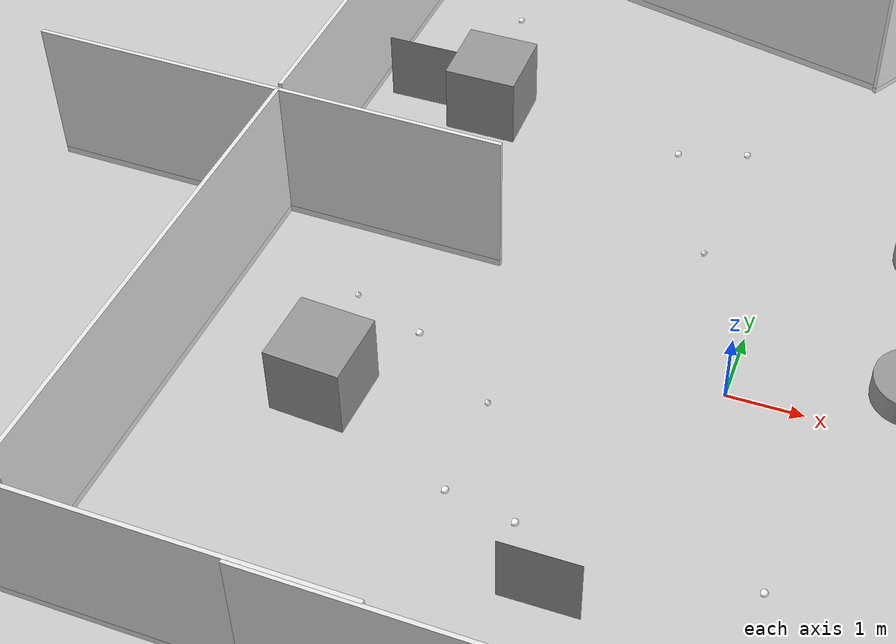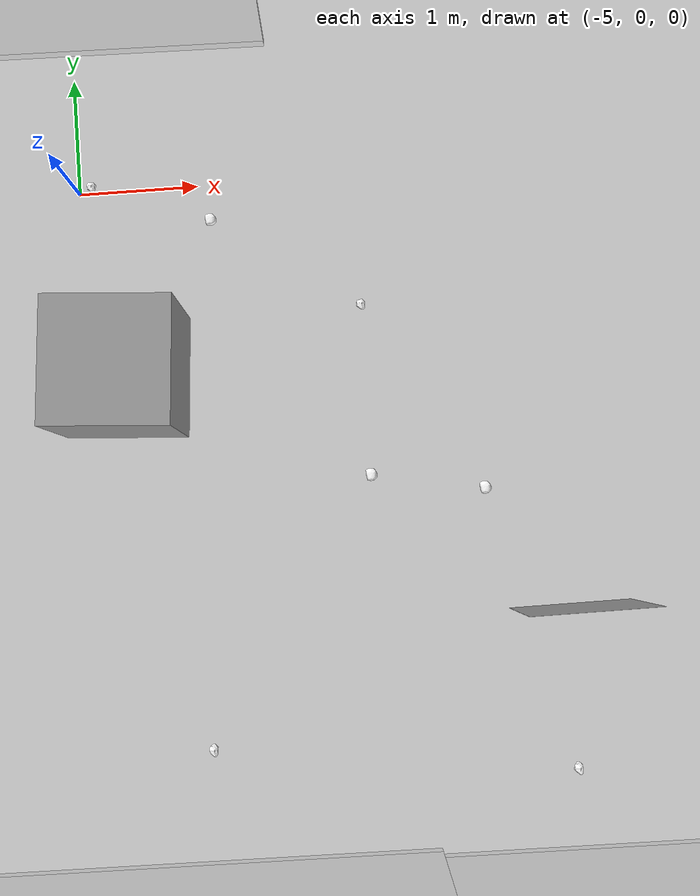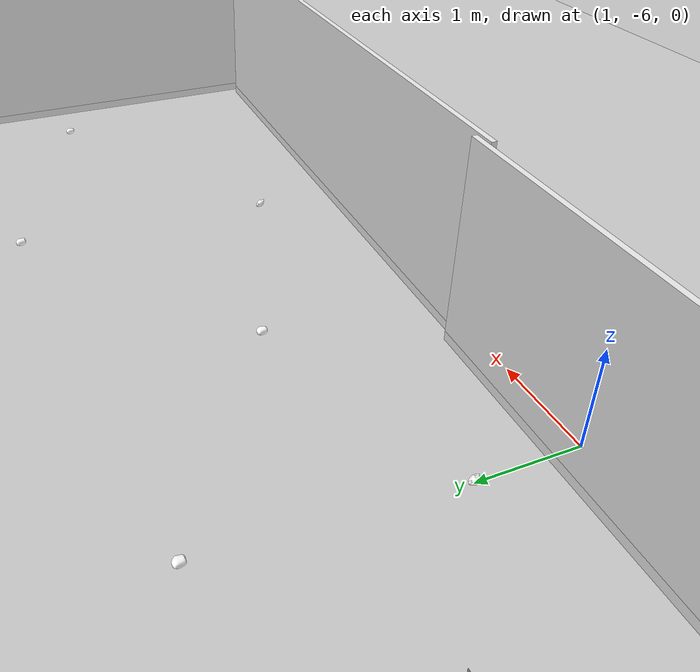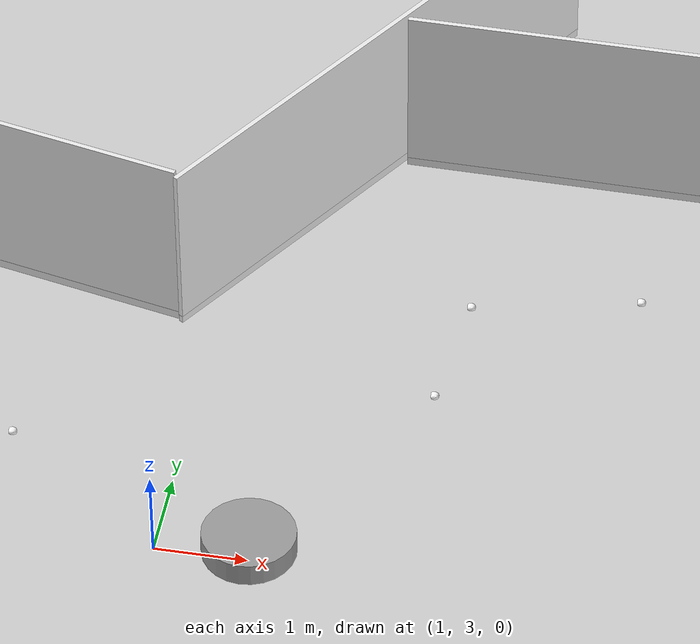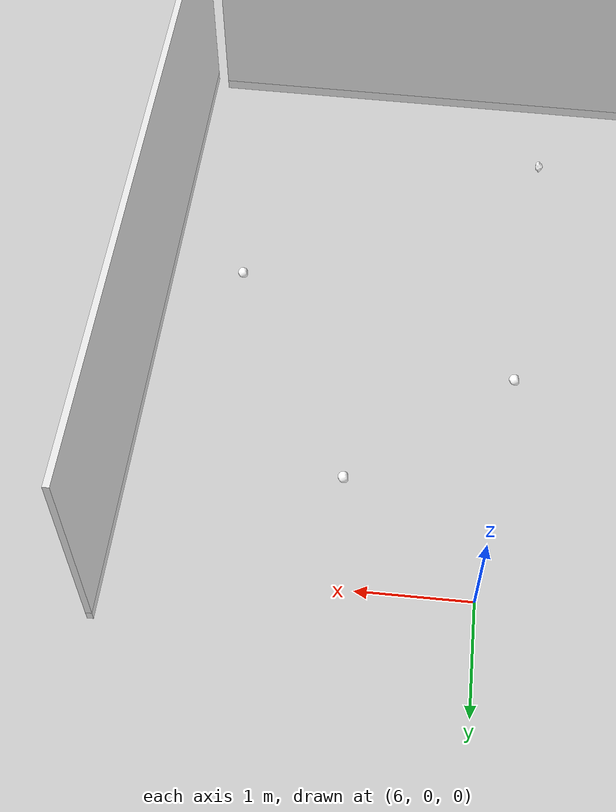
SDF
<sdf version="1.7">
 <world name="default">
  <model name="ground_plane">
   <static>1</static>
   <link name="link">
    <collision name="collision">
     <geometry><plane><normal>0 0 1</normal><size>100 100</size></plane></geometry>
     <surface><friction><ode><mu>100</mu><mu2>50</mu2></ode></friction></surface>
    </collision>
    <visual name="visual">
     <cast_shadows>0</cast_shadows>
     <geometry><plane><normal>0 0 1</normal><size>100 100</size></plane></geometry>
     <material>
      <script><uri>file://media/materials/scripts/gazebo.material</uri><name>Gazebo/Grey</name></script>
     </material>
    </visual>
   </link>
  </model>
  <light name="sun" type="directional">
   <pose>0 0 10 0 -0 0</pose>
   <diffuse>0.8 0.8 0.8 1</diffuse>
   <specular>0.2 0.2 0.2 1</specular>
   <attenuation>
    <range>1000</range>
    <constant>0.9</constant>
    <linear>0.01</linear>
    <quadratic>0.001</quadratic>
   </attenuation>
   <direction>-0.5 0.1 -0.9</direction>
   <spot><inner_angle>0</inner_angle><outer_angle>0</outer_angle><falloff>0</falloff></spot>
  </light>
  <gravity>0 0 -9.8</gravity>
  <magnetic_field>6e-06 2.3e-05 -4.2e-05</magnetic_field>
  <atmosphere type="adiabatic"/>
  <physics name="default_physics" default="0" type="ode">
   <max_step_size>0.001</max_step_size>
   <real_time_factor>1</real_time_factor>
   <real_time_update_rate>1000</real_time_update_rate>
  </physics>
  <scene><ambient>0.4 0.4 0.4 1</ambient><background>0.7 0.7 0.7 1</background><shadows>1</shadows></scene>
  <spherical_coordinates>
   <surface_model>EARTH_WGS84</surface_model>
   <latitude_deg>0</latitude_deg>
   <longitude_deg>0</longitude_deg>
   <elevation>0</elevation>
   <heading_deg>0</heading_deg>
  </spherical_coordinates>
  <model name="night_dome">
   <link name="link">
    <inertial>
     <mass>57.7556</mass>
     <inertia><ixx>147184</ixx><ixy>0</ixy><ixz>0</ixz><iyy>52407.2</iyy><iyz>0</iyz><izz>199581</izz></inertia>
    </inertial>
    <pose>-2.93214 -4.77575 19.3059 0 0.050226 0</pose>
    <visual name="visual">
     <geometry><box><size>104.344 174.871 1</size></box></geometry>
     <material>
      <script><name>Gazebo/Grey</name><uri>file://media/materials/scripts/gazebo.material</uri></script>
      <shader type="pixel"><normal_map>__default__</normal_map></shader>
      <ambient>0 0 0 1</ambient>
      <diffuse>0 0 0 1</diffuse>
      <specular>0.01 0.01 0.01 1</specular>
      <emissive>0 0 0 1</emissive>
     </material>
    </visual>
    <collision name="collision">
     <geometry><box><size>104.344 174.871 1</size></box></geometry>
     <surface>
      <friction>
       <ode><mu>1</mu><mu2>1</mu2><fdir1>0 0 0</fdir1><slip1>0</slip1><slip2>0</slip2></ode>
       <torsional>
        <coefficient>1</coefficient>
        <patch_radius>0</patch_radius>
        <surface_radius>0</surface_radius>
        <use_patch_radius>1</use_patch_radius>
        <ode><slip>0</slip></ode>
       </torsional>
      </friction>
      <bounce><restitution_coefficient>0</restitution_coefficient><threshold>1e+06</threshold></bounce>
      <contact>
       <collide_without_contact>0</collide_without_contact>
       <collide_without_contact_bitmask>1</collide_without_contact_bitmask>
       <collide_bitmask>1</collide_bitmask>
       <ode>
        <soft_cfm>0</soft_cfm>
        <soft_erp>0.2</soft_erp>
        <kp>1e+13</kp>
        <kd>1</kd>
        <max_vel>0.01</max_vel>
        <min_depth>0</min_depth>
       </ode>
       <bullet>
        <split_impulse>1</split_impulse>
        <split_impulse_penetration_threshold>-0.01</split_impulse_penetration_threshold>
        <soft_cfm>0</soft_cfm>
        <soft_erp>0.2</soft_erp>
        <kp>1e+13</kp>
        <kd>1</kd>
       </bullet>
      </contact>
     </surface>
    </collision>
   </link>
   <link name="link_0">
    <inertial>
     <mass>0.0631323</mass>
     <inertia>
      <ixx>0.00100097</ixx>
      <ixy>0</ixy>
      <ixz>0</ixz>
      <iyy>0.00100097</iyy>
      <iyz>0</iyz>
      <izz>0.00100097</izz>
     </inertia>
    </inertial>
    <pose>-0.275814 -5.89028 17.1065 0 0.052806 0</pose>
    <visual name="visual">
     <geometry><sphere><radius>0.199093</radius></sphere></geometry>
     <material>
      <lighting>1</lighting>
      <script><uri>file://media/materials/scripts/gazebo.material</uri><name>Gazebo/Grey</name></script>
      <shader type="pixel"><normal_map>__default__</normal_map></shader>
      <ambient>1 1 1 1</ambient>
      <diffuse>1 1 1 1</diffuse>
      <specular>0.01 0.01 0.01 1</specular>
      <emissive>1 1 1 1</emissive>
     </material>
    </visual>
    <collision name="collision">
     <geometry><sphere><radius>0.199093</radius></sphere></geometry>
     <surface>
      <friction>
       <ode><mu>1</mu><mu2>1</mu2><fdir1>0 0 0</fdir1><slip1>0</slip1><slip2>0</slip2></ode>
       <torsional>
        <coefficient>1</coefficient>
        <patch_radius>0</patch_radius>
        <surface_radius>0</surface_radius>
        <use_patch_radius>1</use_patch_radius>
        <ode><slip>0</slip></ode>
       </torsional>
      </friction>
      <bounce><restitution_coefficient>0</restitution_coefficient><threshold>1e+06</threshold></bounce>
      <contact>
       <collide_without_contact>0</collide_without_contact>
       <collide_without_contact_bitmask>1</collide_without_contact_bitmask>
       <collide_bitmask>1</collide_bitmask>
       <ode>
        <soft_cfm>0</soft_cfm>
        <soft_erp>0.2</soft_erp>
        <kp>1e+13</kp>
        <kd>1</kd>
        <max_vel>0.01</max_vel>
        <min_depth>0</min_depth>
       </ode>
       <bullet>
        <split_impulse>1</split_impulse>
        <split_impulse_penetration_threshold>-0.01</split_impulse_penetration_threshold>
        <soft_cfm>0</soft_cfm>
        <soft_erp>0.2</soft_erp>
        <kp>1e+13</kp>
        <kd>1</kd>
       </bullet>
      </contact>
     </surface>
    </collision>
   </link>
   <link name="link_0_clone">
    <inertial>
     <mass>0.0179938</mass>
     <inertia>
      <ixx>0.000123558</ixx>
      <ixy>0</ixy>
      <ixz>0</ixz>
      <iyy>0.000123558</iyy>
      <iyz>0</iyz>
      <izz>0.000123558</izz>
     </inertia>
    </inertial>
    <pose>-8.62494 -0.833531 17.5302 0 0.105612 0</pose>
    <visual name="visual">
     <geometry><sphere><radius>0.131022</radius></sphere></geometry>
     <material>
      <lighting>1</lighting>
      <script><uri>file://media/materials/scripts/gazebo.material</uri><name>Gazebo/Grey</name></script>
      <shader type="pixel"><normal_map>__default__</normal_map></shader>
      <ambient>1 1 1 1</ambient>
      <diffuse>1 1 1 1</diffuse>
      <specular>0.01 0.01 0.01 1</specular>
      <emissive>1 1 1 1</emissive>
     </material>
    </visual>
    <collision name="collision">
     <geometry><sphere><radius>0.131022</radius></sphere></geometry>
     <surface>
      <friction>
       <ode><mu>1</mu><mu2>1</mu2><fdir1>0 0 0</fdir1><slip1>0</slip1><slip2>0</slip2></ode>
       <torsional>
        <coefficient>1</coefficient>
        <patch_radius>0</patch_radius>
        <surface_radius>0</surface_radius>
        <use_patch_radius>1</use_patch_radius>
        <ode><slip>0</slip></ode>
       </torsional>
      </friction>
      <bounce><restitution_coefficient>0</restitution_coefficient><threshold>1e+06</threshold></bounce>
      <contact>
       <collide_without_contact>0</collide_without_contact>
       <collide_without_contact_bitmask>1</collide_without_contact_bitmask>
       <collide_bitmask>1</collide_bitmask>
       <ode>
        <soft_cfm>0</soft_cfm>
        <soft_erp>0.2</soft_erp>
        <kp>1e+13</kp>
        <kd>1</kd>
        <max_vel>0.01</max_vel>
        <min_depth>0</min_depth>
       </ode>
       <bullet>
        <split_impulse>1</split_impulse>
        <split_impulse_penetration_threshold>-0.01</split_impulse_penetration_threshold>
        <soft_cfm>0</soft_cfm>
        <soft_erp>0.2</soft_erp>
        <kp>1e+13</kp>
        <kd>1</kd>
       </bullet>
      </contact>
     </surface>
    </collision>
   </link>
   <link name="link_0_clone_0">
    <inertial>
     <mass>0.0494736</mass>
     <inertia>
      <ixx>0.000666725</ixx>
      <ixy>0</ixy>
      <ixz>0</ixz>
      <iyy>0.000666725</iyy>
      <iyz>0</iyz>
      <izz>0.000666725</izz>
     </inertia>
    </inertial>
    <pose>-2.71759 -2.86847 16.2038 0 0.105612 0</pose>
    <visual name="visual">
     <geometry><sphere><radius>0.183551</radius></sphere></geometry>
     <material>
      <lighting>1</lighting>
      <script><uri>file://media/materials/scripts/gazebo.material</uri><name>Gazebo/Grey</name></script>
      <shader type="pixel"><normal_map>__default__</normal_map></shader>
      <ambient>1 1 1 1</ambient>
      <diffuse>1 1 1 1</diffuse>
      <specular>0.01 0.01 0.01 1</specular>
      <emissive>1 1 1 1</emissive>
     </material>
    </visual>
    <collision name="collision">
     <geometry><sphere><radius>0.183551</radius></sphere></geometry>
     <surface>
      <friction>
       <ode><mu>1</mu><mu2>1</mu2><fdir1>0 0 0</fdir1><slip1>0</slip1><slip2>0</slip2></ode>
       <torsional>
        <coefficient>1</coefficient>
        <patch_radius>0</patch_radius>
        <surface_radius>0</surface_radius>
        <use_patch_radius>1</use_patch_radius>
        <ode><slip>0</slip></ode>
       </torsional>
      </friction>
      <bounce><restitution_coefficient>0</restitution_coefficient><threshold>1e+06</threshold></bounce>
      <contact>
       <collide_without_contact>0</collide_without_contact>
       <collide_without_contact_bitmask>1</collide_without_contact_bitmask>
       <collide_bitmask>1</collide_bitmask>
       <ode>
        <soft_cfm>0</soft_cfm>
        <soft_erp>0.2</soft_erp>
        <kp>1e+13</kp>
        <kd>1</kd>
        <max_vel>0.01</max_vel>
        <min_depth>0</min_depth>
       </ode>
       <bullet>
        <split_impulse>1</split_impulse>
        <split_impulse_penetration_threshold>-0.01</split_impulse_penetration_threshold>
        <soft_cfm>0</soft_cfm>
        <soft_erp>0.2</soft_erp>
        <kp>1e+13</kp>
        <kd>1</kd>
       </bullet>
      </contact>
     </surface>
    </collision>
   </link>
   <link name="link_0_clone_0_clone">
    <inertial>
     <mass>0.00559209</mass>
     <inertia>
      <ixx>1.76172e-05</ixx>
      <ixy>0</ixy>
      <ixz>0</ixz>
      <iyy>1.76172e-05</iyy>
      <iyz>0</iyz>
      <izz>1.76172e-05</izz>
     </inertia>
    </inertial>
    <pose>-8.85838 2.24926 16.6946 0 0.158418 0</pose>
    <visual name="visual">
     <geometry><sphere><radius>0.0887467</radius></sphere></geometry>
     <material>
      <lighting>1</lighting>
      <script><uri>file://media/materials/scripts/gazebo.material</uri><name>Gazebo/Grey</name></script>
      <shader type="pixel"><normal_map>__default__</normal_map></shader>
      <ambient>1 1 1 1</ambient>
      <diffuse>1 1 1 1</diffuse>
      <specular>0.01 0.01 0.01 1</specular>
      <emissive>1 1 1 1</emissive>
     </material>
    </visual>
    <collision name="collision">
     <geometry><sphere><radius>0.088747</radius></sphere></geometry>
     <surface>
      <friction>
       <ode><mu>1</mu><mu2>1</mu2><fdir1>0 0 0</fdir1><slip1>0</slip1><slip2>0</slip2></ode>
       <torsional>
        <coefficient>1</coefficient>
        <patch_radius>0</patch_radius>
        <surface_radius>0</surface_radius>
        <use_patch_radius>1</use_patch_radius>
        <ode><slip>0</slip></ode>
       </torsional>
      </friction>
      <bounce><restitution_coefficient>0</restitution_coefficient><threshold>1e+06</threshold></bounce>
      <contact>
       <collide_without_contact>0</collide_without_contact>
       <collide_without_contact_bitmask>1</collide_without_contact_bitmask>
       <collide_bitmask>1</collide_bitmask>
       <ode>
        <soft_cfm>0</soft_cfm>
        <soft_erp>0.2</soft_erp>
        <kp>1e+13</kp>
        <kd>1</kd>
        <max_vel>0.01</max_vel>
        <min_depth>0</min_depth>
       </ode>
       <bullet>
        <split_impulse>1</split_impulse>
        <split_impulse_penetration_threshold>-0.01</split_impulse_penetration_threshold>
        <soft_cfm>0</soft_cfm>
        <soft_erp>0.2</soft_erp>
        <kp>1e+13</kp>
        <kd>1</kd>
       </bullet>
      </contact>
     </surface>
    </collision>
   </link>
   <link name="link_0_clone_0_clone_0">
    <inertial>
     <mass>0.00122686</mass>
     <inertia>
      <ixx>1.40568e-06</ixx>
      <ixy>0</ixy>
      <ixz>0</ixz>
      <iyy>1.40568e-06</iyy>
      <iyz>0</iyz>
      <izz>1.40568e-06</izz>
     </inertia>
    </inertial>
    <pose>-10.2143 -5.3147 16.7663 0 0.158418 0</pose>
    <visual name="visual">
     <geometry><sphere><radius>0.0535201</radius></sphere></geometry>
     <material>
      <lighting>1</lighting>
      <script><uri>file://media/materials/scripts/gazebo.material</uri><name>Gazebo/Grey</name></script>
      <shader type="pixel"><normal_map>__default__</normal_map></shader>
      <ambient>1 1 1 1</ambient>
      <diffuse>1 1 1 1</diffuse>
      <specular>0.01 0.01 0.01 1</specular>
      <emissive>1 1 1 1</emissive>
     </material>
    </visual>
    <collision name="collision">
     <geometry><sphere><radius>0.05352</radius></sphere></geometry>
     <surface>
      <friction>
       <ode><mu>1</mu><mu2>1</mu2><fdir1>0 0 0</fdir1><slip1>0</slip1><slip2>0</slip2></ode>
       <torsional>
        <coefficient>1</coefficient>
        <patch_radius>0</patch_radius>
        <surface_radius>0</surface_radius>
        <use_patch_radius>1</use_patch_radius>
        <ode><slip>0</slip></ode>
       </torsional>
      </friction>
      <bounce><restitution_coefficient>0</restitution_coefficient><threshold>1e+06</threshold></bounce>
      <contact>
       <collide_without_contact>0</collide_without_contact>
       <collide_without_contact_bitmask>1</collide_without_contact_bitmask>
       <collide_bitmask>1</collide_bitmask>
       <ode>
        <soft_cfm>0</soft_cfm>
        <soft_erp>0.2</soft_erp>
        <kp>1e+13</kp>
        <kd>1</kd>
        <max_vel>0.01</max_vel>
        <min_depth>0</min_depth>
       </ode>
       <bullet>
        <split_impulse>1</split_impulse>
        <split_impulse_penetration_threshold>-0.01</split_impulse_penetration_threshold>
        <soft_cfm>0</soft_cfm>
        <soft_erp>0.2</soft_erp>
        <kp>1e+13</kp>
        <kd>1</kd>
       </bullet>
      </contact>
     </surface>
    </collision>
   </link>
   <link name="link_0_clone_0_clone_1">
    <inertial>
     <mass>0.00818638</mass>
     <inertia>
      <ixx>3.32509e-05</ixx>
      <ixy>0</ixy>
      <ixz>0</ixz>
      <iyy>3.32509e-05</iyy>
      <iyz>0</iyz>
      <izz>3.32509e-05</izz>
     </inertia>
    </inertial>
    <pose>-11.6715 1.25097 16.8434 0 0.158418 0</pose>
    <visual name="visual">
     <geometry><sphere><radius>0.100769</radius></sphere></geometry>
     <material>
      <lighting>1</lighting>
      <script><uri>file://media/materials/scripts/gazebo.material</uri><name>Gazebo/Grey</name></script>
      <shader type="pixel"><normal_map>__default__</normal_map></shader>
      <ambient>1 1 1 1</ambient>
      <diffuse>1 1 1 1</diffuse>
      <specular>0.01 0.01 0.01 1</specular>
      <emissive>1 1 1 1</emissive>
     </material>
    </visual>
    <collision name="collision">
     <geometry><sphere><radius>0.100769</radius></sphere></geometry>
     <surface>
      <friction>
       <ode><mu>1</mu><mu2>1</mu2><fdir1>0 0 0</fdir1><slip1>0</slip1><slip2>0</slip2></ode>
       <torsional>
        <coefficient>1</coefficient>
        <patch_radius>0</patch_radius>
        <surface_radius>0</surface_radius>
        <use_patch_radius>1</use_patch_radius>
        <ode><slip>0</slip></ode>
       </torsional>
      </friction>
      <bounce><restitution_coefficient>0</restitution_coefficient><threshold>1e+06</threshold></bounce>
      <contact>
       <collide_without_contact>0</collide_without_contact>
       <collide_without_contact_bitmask>1</collide_without_contact_bitmask>
       <collide_bitmask>1</collide_bitmask>
       <ode>
        <soft_cfm>0</soft_cfm>
        <soft_erp>0.2</soft_erp>
        <kp>1e+13</kp>
        <kd>1</kd>
        <max_vel>0.01</max_vel>
        <min_depth>0</min_depth>
       </ode>
       <bullet>
        <split_impulse>1</split_impulse>
        <split_impulse_penetration_threshold>-0.01</split_impulse_penetration_threshold>
        <soft_cfm>0</soft_cfm>
        <soft_erp>0.2</soft_erp>
        <kp>1e+13</kp>
        <kd>1</kd>
       </bullet>
      </contact>
     </surface>
    </collision>
   </link>
   <link name="link_0_clone_0_clone_2">
    <inertial>
     <mass>0.574459</mass>
     <inertia>
      <ixx>0.0396967</ixx>
      <ixy>0</ixy>
      <ixz>0</ixz>
      <iyy>0.0396967</iyy>
      <iyz>0</iyz>
      <izz>0.0396967</izz>
     </inertia>
    </inertial>
    <pose>-8.35253 -8.50246 16.6679 0 0.158418 0</pose>
    <visual name="visual">
     <geometry><sphere><radius>0.41564</radius></sphere></geometry>
     <material>
      <lighting>1</lighting>
      <script><uri>file://media/materials/scripts/gazebo.material</uri><name>Gazebo/Grey</name></script>
      <shader type="pixel"><normal_map>__default__</normal_map></shader>
      <ambient>1 1 1 1</ambient>
      <diffuse>1 1 1 1</diffuse>
      <specular>0.01 0.01 0.01 1</specular>
      <emissive>1 1 1 1</emissive>
     </material>
    </visual>
    <collision name="collision">
     <geometry><sphere><radius>0.41564</radius></sphere></geometry>
     <surface>
      <friction>
       <ode><mu>1</mu><mu2>1</mu2><fdir1>0 0 0</fdir1><slip1>0</slip1><slip2>0</slip2></ode>
       <torsional>
        <coefficient>1</coefficient>
        <patch_radius>0</patch_radius>
        <surface_radius>0</surface_radius>
        <use_patch_radius>1</use_patch_radius>
        <ode><slip>0</slip></ode>
       </torsional>
      </friction>
      <bounce><restitution_coefficient>0</restitution_coefficient><threshold>1e+06</threshold></bounce>
      <contact>
       <collide_without_contact>0</collide_without_contact>
       <collide_without_contact_bitmask>1</collide_without_contact_bitmask>
       <collide_bitmask>1</collide_bitmask>
       <ode>
        <soft_cfm>0</soft_cfm>
        <soft_erp>0.2</soft_erp>
        <kp>1e+13</kp>
        <kd>1</kd>
        <max_vel>0.01</max_vel>
        <min_depth>0</min_depth>
       </ode>
       <bullet>
        <split_impulse>1</split_impulse>
        <split_impulse_penetration_threshold>-0.01</split_impulse_penetration_threshold>
        <soft_cfm>0</soft_cfm>
        <soft_erp>0.2</soft_erp>
        <kp>1e+13</kp>
        <kd>1</kd>
       </bullet>
      </contact>
     </surface>
    </collision>
   </link>
   <link name="link_0_clone_0_clone_3">
    <inertial>
     <mass>0.0494736</mass>
     <inertia>
      <ixx>0.000666725</ixx>
      <ixy>0</ixy>
      <ixz>0</ixz>
      <iyy>0.000666725</iyy>
      <iyz>0</iyz>
      <izz>0.000666725</izz>
     </inertia>
    </inertial>
    <pose>-3.53218 4.21829 16.4131 0 0.158418 0</pose>
    <visual name="visual">
     <geometry><sphere><radius>0.183551</radius></sphere></geometry>
     <material>
      <lighting>1</lighting>
      <script><uri>file://media/materials/scripts/gazebo.material</uri><name>Gazebo/Grey</name></script>
      <shader type="pixel"><normal_map>__default__</normal_map></shader>
      <ambient>1 1 1 1</ambient>
      <diffuse>1 1 1 1</diffuse>
      <specular>0.01 0.01 0.01 1</specular>
      <emissive>1 1 1 1</emissive>
     </material>
    </visual>
    <collision name="collision">
     <geometry><sphere><radius>0.183551</radius></sphere></geometry>
     <surface>
      <friction>
       <ode><mu>1</mu><mu2>1</mu2><fdir1>0 0 0</fdir1><slip1>0</slip1><slip2>0</slip2></ode>
       <torsional>
        <coefficient>1</coefficient>
        <patch_radius>0</patch_radius>
        <surface_radius>0</surface_radius>
        <use_patch_radius>1</use_patch_radius>
        <ode><slip>0</slip></ode>
       </torsional>
      </friction>
      <bounce><restitution_coefficient>0</restitution_coefficient><threshold>1e+06</threshold></bounce>
      <contact>
       <collide_without_contact>0</collide_without_contact>
       <collide_without_contact_bitmask>1</collide_without_contact_bitmask>
       <collide_bitmask>1</collide_bitmask>
       <ode>
        <soft_cfm>0</soft_cfm>
        <soft_erp>0.2</soft_erp>
        <kp>1e+13</kp>
        <kd>1</kd>
        <max_vel>0.01</max_vel>
        <min_depth>0</min_depth>
       </ode>
       <bullet>
        <split_impulse>1</split_impulse>
        <split_impulse_penetration_threshold>-0.01</split_impulse_penetration_threshold>
        <soft_cfm>0</soft_cfm>
        <soft_erp>0.2</soft_erp>
        <kp>1e+13</kp>
        <kd>1</kd>
       </bullet>
      </contact>
     </surface>
    </collision>
   </link>
   <link name="link_0_clone_0_clone_3_clone">
    <inertial>
     <mass>0.0190842</mass>
     <inertia>
      <ixx>0.000136285</ixx>
      <ixy>0</ixy>
      <ixz>0</ixz>
      <iyy>0.000136285</iyy>
      <iyz>0</iyz>
      <izz>0.000136285</izz>
     </inertia>
    </inertial>
    <pose>-5.55986 -1.56577 16.7299 0 0.211224 0</pose>
    <visual name="visual">
     <geometry><sphere><radius>0.133616</radius></sphere></geometry>
     <material>
      <lighting>1</lighting>
      <script><uri>file://media/materials/scripts/gazebo.material</uri><name>Gazebo/Grey</name></script>
      <shader type="pixel"><normal_map>__default__</normal_map></shader>
      <ambient>1 1 1 1</ambient>
      <diffuse>1 1 1 1</diffuse>
      <specular>0.01 0.01 0.01 1</specular>
      <emissive>1 1 1 1</emissive>
     </material>
    </visual>
    <collision name="collision">
     <geometry><sphere><radius>0.133616</radius></sphere></geometry>
     <surface>
      <friction>
       <ode><mu>1</mu><mu2>1</mu2><fdir1>0 0 0</fdir1><slip1>0</slip1><slip2>0</slip2></ode>
       <torsional>
        <coefficient>1</coefficient>
        <patch_radius>0</patch_radius>
        <surface_radius>0</surface_radius>
        <use_patch_radius>1</use_patch_radius>
        <ode><slip>0</slip></ode>
       </torsional>
      </friction>
      <bounce><restitution_coefficient>0</restitution_coefficient><threshold>1e+06</threshold></bounce>
      <contact>
       <collide_without_contact>0</collide_without_contact>
       <collide_without_contact_bitmask>1</collide_without_contact_bitmask>
       <collide_bitmask>1</collide_bitmask>
       <ode>
        <soft_cfm>0</soft_cfm>
        <soft_erp>0.2</soft_erp>
        <kp>1e+13</kp>
        <kd>1</kd>
        <max_vel>0.01</max_vel>
        <min_depth>0</min_depth>
       </ode>
       <bullet>
        <split_impulse>1</split_impulse>
        <split_impulse_penetration_threshold>-0.01</split_impulse_penetration_threshold>
        <soft_cfm>0</soft_cfm>
        <soft_erp>0.2</soft_erp>
        <kp>1e+13</kp>
        <kd>1</kd>
       </bullet>
      </contact>
     </surface>
    </collision>
   </link>
   <link name="link_0_clone_0_clone_3_clone_0">
    <inertial>
     <mass>0.0494736</mass>
     <inertia>
      <ixx>0.000666725</ixx>
      <ixy>0</ixy>
      <ixz>0</ixz>
      <iyy>0.000666725</iyy>
      <iyz>0</iyz>
      <izz>0.000666725</izz>
     </inertia>
    </inertial>
    <pose>0.869266 0.493087 16.3901 0 0.211224 0</pose>
    <visual name="visual">
     <geometry><sphere><radius>0.183551</radius></sphere></geometry>
     <material>
      <lighting>1</lighting>
      <script><uri>file://media/materials/scripts/gazebo.material</uri><name>Gazebo/Grey</name></script>
      <shader type="pixel"><normal_map>__default__</normal_map></shader>
      <ambient>1 1 1 1</ambient>
      <diffuse>1 1 1 1</diffuse>
      <specular>0.01 0.01 0.01 1</specular>
      <emissive>1 1 1 1</emissive>
     </material>
    </visual>
    <collision name="collision">
     <geometry><sphere><radius>0.183551</radius></sphere></geometry>
     <surface>
      <friction>
       <ode><mu>1</mu><mu2>1</mu2><fdir1>0 0 0</fdir1><slip1>0</slip1><slip2>0</slip2></ode>
       <torsional>
        <coefficient>1</coefficient>
        <patch_radius>0</patch_radius>
        <surface_radius>0</surface_radius>
        <use_patch_radius>1</use_patch_radius>
        <ode><slip>0</slip></ode>
       </torsional>
      </friction>
      <bounce><restitution_coefficient>0</restitution_coefficient><threshold>1e+06</threshold></bounce>
      <contact>
       <collide_without_contact>0</collide_without_contact>
       <collide_without_contact_bitmask>1</collide_without_contact_bitmask>
       <collide_bitmask>1</collide_bitmask>
       <ode>
        <soft_cfm>0</soft_cfm>
        <soft_erp>0.2</soft_erp>
        <kp>1e+13</kp>
        <kd>1</kd>
        <max_vel>0.01</max_vel>
        <min_depth>0</min_depth>
       </ode>
       <bullet>
        <split_impulse>1</split_impulse>
        <split_impulse_penetration_threshold>-0.01</split_impulse_penetration_threshold>
        <soft_cfm>0</soft_cfm>
        <soft_erp>0.2</soft_erp>
        <kp>1e+13</kp>
        <kd>1</kd>
       </bullet>
      </contact>
     </surface>
    </collision>
   </link>
   <link name="link_0_clone_0_clone_3_clone_1">
    <inertial>
     <mass>0.0494736</mass>
     <inertia>
      <ixx>0.000666725</ixx>
      <ixy>0</ixy>
      <ixz>0</ixz>
      <iyy>0.000666725</iyy>
      <iyz>0</iyz>
      <izz>0.000666725</izz>
     </inertia>
    </inertial>
    <pose>-4.11111 1.16471 16.6533 0 0.211224 0</pose>
    <visual name="visual">
     <geometry><sphere><radius>0.183551</radius></sphere></geometry>
     <material>
      <lighting>1</lighting>
      <script><uri>file://media/materials/scripts/gazebo.material</uri><name>Gazebo/Grey</name></script>
      <shader type="pixel"><normal_map>__default__</normal_map></shader>
      <ambient>1 1 1 1</ambient>
      <diffuse>1 1 1 1</diffuse>
      <specular>0.01 0.01 0.01 1</specular>
      <emissive>1 1 1 1</emissive>
     </material>
    </visual>
    <collision name="collision">
     <geometry><sphere><radius>0.183551</radius></sphere></geometry>
     <surface>
      <friction>
       <ode><mu>1</mu><mu2>1</mu2><fdir1>0 0 0</fdir1><slip1>0</slip1><slip2>0</slip2></ode>
       <torsional>
        <coefficient>1</coefficient>
        <patch_radius>0</patch_radius>
        <surface_radius>0</surface_radius>
        <use_patch_radius>1</use_patch_radius>
        <ode><slip>0</slip></ode>
       </torsional>
      </friction>
      <bounce><restitution_coefficient>0</restitution_coefficient><threshold>1e+06</threshold></bounce>
      <contact>
       <collide_without_contact>0</collide_without_contact>
       <collide_without_contact_bitmask>1</collide_without_contact_bitmask>
       <collide_bitmask>1</collide_bitmask>
       <ode>
        <soft_cfm>0</soft_cfm>
        <soft_erp>0.2</soft_erp>
        <kp>1e+13</kp>
        <kd>1</kd>
        <max_vel>0.01</max_vel>
        <min_depth>0</min_depth>
       </ode>
       <bullet>
        <split_impulse>1</split_impulse>
        <split_impulse_penetration_threshold>-0.01</split_impulse_penetration_threshold>
        <soft_cfm>0</soft_cfm>
        <soft_erp>0.2</soft_erp>
        <kp>1e+13</kp>
        <kd>1</kd>
       </bullet>
      </contact>
     </surface>
    </collision>
   </link>
   <link name="link_0_clone_0_clone_3_clone_2">
    <inertial>
     <mass>0.00427312</mass>
     <inertia>
      <ixx>1.1252e-05</ixx>
      <ixy>0</ixy>
      <ixz>0</ixz>
      <iyy>1.1252e-05</iyy>
      <iyz>0</iyz>
      <izz>1.1252e-05</izz>
     </inertia>
    </inertial>
    <pose>-4.30409 -7.19512 16.6635 0 0.211224 0</pose>
    <visual name="visual">
     <geometry><sphere><radius>0.0811356</radius></sphere></geometry>
     <material>
      <lighting>1</lighting>
      <script><uri>file://media/materials/scripts/gazebo.material</uri><name>Gazebo/Grey</name></script>
      <shader type="pixel"><normal_map>__default__</normal_map></shader>
      <ambient>1 1 1 1</ambient>
      <diffuse>1 1 1 1</diffuse>
      <specular>0.01 0.01 0.01 1</specular>
      <emissive>1 1 1 1</emissive>
     </material>
    </visual>
    <collision name="collision">
     <geometry><sphere><radius>0.081136</radius></sphere></geometry>
     <surface>
      <friction>
       <ode><mu>1</mu><mu2>1</mu2><fdir1>0 0 0</fdir1><slip1>0</slip1><slip2>0</slip2></ode>
       <torsional>
        <coefficient>1</coefficient>
        <patch_radius>0</patch_radius>
        <surface_radius>0</surface_radius>
        <use_patch_radius>1</use_patch_radius>
        <ode><slip>0</slip></ode>
       </torsional>
      </friction>
      <bounce><restitution_coefficient>0</restitution_coefficient><threshold>1e+06</threshold></bounce>
      <contact>
       <collide_without_contact>0</collide_without_contact>
       <collide_without_contact_bitmask>1</collide_without_contact_bitmask>
       <collide_bitmask>1</collide_bitmask>
       <ode>
        <soft_cfm>0</soft_cfm>
        <soft_erp>0.2</soft_erp>
        <kp>1e+13</kp>
        <kd>1</kd>
        <max_vel>0.01</max_vel>
        <min_depth>0</min_depth>
       </ode>
       <bullet>
        <split_impulse>1</split_impulse>
        <split_impulse_penetration_threshold>-0.01</split_impulse_penetration_threshold>
        <soft_cfm>0</soft_cfm>
        <soft_erp>0.2</soft_erp>
        <kp>1e+13</kp>
        <kd>1</kd>
       </bullet>
      </contact>
     </surface>
    </collision>
   </link>
   <static>1</static>
   <pose>7.21328 -0.05966 40.6775 0 -0 0</pose>
  </model>
  <model name="unit_cylinder">
   <pose>2.14694 0.738304 0.175627 0 -0 2.7e-05</pose>
   <link name="link">
    <inertial>
     <mass>1</mass>
     <inertia><ixx>0.145833</ixx><ixy>0</ixy><ixz>0</ixz><iyy>0.145833</iyy><iyz>0</iyz><izz>0.125</izz></inertia>
    </inertial>
    <collision name="collision">
     <geometry><cylinder><radius>0.5</radius><length>0.351255</length></cylinder></geometry>
    </collision>
    <visual name="visual">
     <geometry><cylinder><radius>0.5</radius><length>0.351255</length></cylinder></geometry>
     <material>
      <script><name>Gazebo/Grey</name><uri>file://media/materials/scripts/gazebo.material</uri></script>
     </material>
    </visual>
   </link>
  </model>
  <model name="unit_cylinder_0">
   <pose>1.98294 3.15713 0.130238 0 0 -0.02272</pose>
   <link name="link">
    <inertial>
     <mass>1</mass>
     <inertia><ixx>0.145833</ixx><ixy>0</ixy><ixz>0</ixz><iyy>0.145833</iyy><iyz>0</iyz><izz>0.125</izz></inertia>
    </inertial>
    <collision name="collision">
     <geometry><cylinder><radius>0.5</radius><length>0.260477</length></cylinder></geometry>
    </collision>
    <visual name="visual">
     <geometry><cylinder><radius>0.5</radius><length>0.260477</length></cylinder></geometry>
     <material>
      <script><name>Gazebo/Grey</name><uri>file://media/materials/scripts/gazebo.material</uri></script>
     </material>
    </visual>
   </link>
  </model>
  <model name="unit_box">
   <pose>-4.50652 4.10936 0.499995 0 -1e-05 -0.008331</pose>
   <link name="link">
    <inertial>
     <mass>1</mass>
     <inertia>
      <ixx>0.166667</ixx>
      <ixy>0</ixy>
      <ixz>0</ixz>
      <iyy>0.166667</iyy>
      <iyz>0</iyz>
      <izz>0.166667</izz>
     </inertia>
    </inertial>
    <collision name="collision"><geometry><box><size>1 1 1</size></box></geometry></collision>
    <visual name="visual">
     <geometry><box><size>1 1 1</size></box></geometry>
     <material>
      <script><name>Gazebo/Grey</name><uri>file://media/materials/scripts/gazebo.material</uri></script>
     </material>
    </visual>
   </link>
  </model>
  <model name="unit_cylinder_1">
   <pose>-2.60305 11.3525 0.000201 1.5708 -1.35369 -3.12185</pose>
   <link name="link">
    <inertial>
     <mass>1</mass>
     <inertia><ixx>0.145833</ixx><ixy>0</ixy><ixz>0</ixz><iyy>0.145833</iyy><iyz>0</iyz><izz>0.125</izz></inertia>
    </inertial>
    <collision name="collision">
     <geometry><cylinder><radius>0.000201114</radius><length>1</length></cylinder></geometry>
    </collision>
    <visual name="visual">
     <geometry><cylinder><radius>0.000201114</radius><length>1</length></cylinder></geometry>
     <material>
      <script><name>Gazebo/Grey</name><uri>file://media/materials/scripts/gazebo.material</uri></script>
     </material>
    </visual>
   </link>
  </model>
  <model name="unit_box_clone">
   <pose>-5.50698 4.0579 0.5 0 0 -0.001181</pose>
   <link name="link">
    <inertial>
     <mass>1</mass>
     <inertia>
      <ixx>0.166667</ixx>
      <ixy>0</ixy>
      <ixz>0</ixz>
      <iyy>0.166667</iyy>
      <iyz>0</iyz>
      <izz>0.166667</izz>
     </inertia>
    </inertial>
    <collision name="collision"><geometry><box><size>1 5.06525e-05 1</size></box></geometry></collision>
    <visual name="visual">
     <geometry><box><size>1 5.06525e-05 1</size></box></geometry>
     <material>
      <script><name>Gazebo/Grey</name><uri>file://media/materials/scripts/gazebo.material</uri></script>
     </material>
    </visual>
   </link>
  </model>
  <model name="unit_box_clone_1">
   <pose>-1.17769 -3.71836 0.5 -2e-06 0 5e-06</pose>
   <link name="link">
    <inertial>
     <mass>1</mass>
     <inertia>
      <ixx>0.166667</ixx>
      <ixy>0</ixy>
      <ixz>0</ixz>
      <iyy>0.166667</iyy>
      <iyz>0</iyz>
      <izz>0.166667</izz>
     </inertia>
    </inertial>
    <collision name="collision"><geometry><box><size>1 0.00159558 1</size></box></geometry></collision>
    <visual name="visual">
     <geometry><box><size>1 0.00159558 1</size></box></geometry>
     <material>
      <script><name>Gazebo/Grey</name><uri>file://media/materials/scripts/gazebo.material</uri></script>
     </material>
    </visual>
   </link>
  </model>
  <model name="unit_box_0">
   <pose>-4.66361 -1.5958 0.5 0 -0 -0.068173</pose>
   <link name="link">
    <inertial>
     <mass>1</mass>
     <inertia>
      <ixx>0.166667</ixx>
      <ixy>0</ixy>
      <ixz>0</ixz>
      <iyy>0.166667</iyy>
      <iyz>0</iyz>
      <izz>0.166667</izz>
     </inertia>
    </inertial>
    <collision name="collision"><geometry><box><size>1 1 1</size></box></geometry></collision>
    <visual name="visual">
     <geometry><box><size>1 1 1</size></box></geometry>
     <material>
      <script><name>Gazebo/Grey</name><uri>file://media/materials/scripts/gazebo.material</uri></script>
     </material>
    </visual>
   </link>
  </model>
  <model name="unit_box_2">
   <pose>-0.068794 -10.6758 0.000268 2.3e-05 1.1e-05 0.91865</pose>
   <link name="link">
    <inertial>
     <mass>1</mass>
     <inertia>
      <ixx>0.166667</ixx>
      <ixy>0</ixy>
      <ixz>0</ixz>
      <iyy>0.166667</iyy>
      <iyz>0</iyz>
      <izz>0.166667</izz>
     </inertia>
    </inertial>
    <collision name="collision">
     <geometry><box><size>0.000679255 0.00248235 0.000536821</size></box></geometry>
    </collision>
    <visual name="visual">
     <geometry><box><size>0.000679255 0.00248235 0.000536821</size></box></geometry>
     <material>
      <script><name>Gazebo/Grey</name><uri>file://media/materials/scripts/gazebo.material</uri></script>
     </material>
    </visual>
   </link>
  </model>
  <model name="full_wall_55_6475_2090">
   <link name="link">
    <inertial>
     <mass>50</mass>
     <inertia><ixx>1</ixx><ixy>0</ixy><ixz>0</ixz><iyy>1</iyy><iyz>0</iyz><izz>1</izz></inertia>
    </inertial>
    <visual name="bottom_frame">
     <pose>0 0 0.05 0 -0 0</pose>
     <geometry><box><size>0.055 6.475 0.1</size></box></geometry>
     <material>
      <script><uri>model://base_materials/color/scripts</uri><name>hsr_color/white</name></script>
     </material>
    </visual>
    <collision name="collision_bottom_frame">
     <pose>0 0 0.05 0 -0 0</pose>
     <geometry><box><size>0.055 6.475 0.1</size></box></geometry>
    </collision>
    <visual name="wall">
     <pose>0 0 1.095 0 -0 0</pose>
     <geometry><box><size>0.055 6.475 1.99</size></box></geometry>
     <material>
      <script>
       <uri>model://base_materials/wall/scripts</uri>
       <uri>model://base_materials/wall/textures</uri>
       <name>wall/white_noise</name>
      </script>
     </material>
    </visual>
    <collision name="collision_wall">
     <pose>0 0 1.095 0 -0 0</pose>
     <geometry><box><size>0.055 6.475 1.99</size></box></geometry>
    </collision>
    <velocity_decay><linear>0</linear><angular>0</angular></velocity_decay>
   </link>
   <static>1</static>
   <pose>9.18279 6.58409 0 0 -0 0</pose>
  </model>
  <model name="full_wall_55_6475_2090_clone">
   <link name="link">
    <inertial>
     <mass>50</mass>
     <inertia><ixx>1</ixx><ixy>0</ixy><ixz>0</ixz><iyy>1</iyy><iyz>0</iyz><izz>1</izz></inertia>
    </inertial>
    <visual name="bottom_frame">
     <pose>0 0 0.05 0 -0 0</pose>
     <geometry><box><size>0.055 6.475 0.1</size></box></geometry>
     <material>
      <script><uri>model://base_materials/color/scripts</uri><name>hsr_color/white</name></script>
     </material>
    </visual>
    <collision name="collision_bottom_frame">
     <pose>0 0 0.05 0 -0 0</pose>
     <geometry><box><size>0.055 6.475 0.1</size></box></geometry>
    </collision>
    <visual name="wall">
     <pose>0 0 1.095 0 -0 0</pose>
     <geometry><box><size>0.055 6.475 1.99</size></box></geometry>
     <material>
      <script>
       <uri>model://base_materials/wall/scripts</uri>
       <uri>model://base_materials/wall/textures</uri>
       <name>wall/white_noise</name>
      </script>
     </material>
    </visual>
    <collision name="collision_wall">
     <pose>0 0 1.095 0 -0 0</pose>
     <geometry><box><size>0.055 6.475 1.99</size></box></geometry>
    </collision>
    <velocity_decay><linear>0</linear><angular>0</angular></velocity_decay>
   </link>
   <static>1</static>
   <pose>2.30458 9.15688 0 -0.007021 0 2.57826</pose>
  </model>
  <model name="full_wall_55_6475_2090_clone_clone">
   <link name="link">
    <inertial>
     <mass>50</mass>
     <inertia><ixx>1</ixx><ixy>0</ixy><ixz>0</ixz><iyy>1</iyy><iyz>0</iyz><izz>1</izz></inertia>
    </inertial>
    <visual name="bottom_frame">
     <pose>0 0 0.05 0 -0 0</pose>
     <geometry><box><size>0.055 6.475 0.1</size></box></geometry>
     <material>
      <script><uri>model://base_materials/color/scripts</uri><name>hsr_color/white</name></script>
     </material>
    </visual>
    <collision name="collision_bottom_frame">
     <pose>0 0 0.05 0 -0 0</pose>
     <geometry><box><size>0.055 6.475 0.1</size></box></geometry>
    </collision>
    <visual name="wall">
     <pose>0 0 1.095 0 -0 0</pose>
     <geometry><box><size>0.055 6.475 1.99</size></box></geometry>
     <material>
      <script>
       <uri>model://base_materials/wall/scripts</uri>
       <uri>model://base_materials/wall/textures</uri>
       <name>wall/white_noise</name>
      </script>
     </material>
    </visual>
    <collision name="collision_wall">
     <pose>0 0 1.095 0 -0 0</pose>
     <geometry><box><size>0.055 6.475 1.99</size></box></geometry>
    </collision>
    <velocity_decay><linear>0</linear><angular>0</angular></velocity_decay>
   </link>
   <static>1</static>
   <pose>9.07571 -2.7786 0 0 -0 3.12864</pose>
  </model>
  <model name="full_wall_55_6475_2090_clone_clone_0">
   <link name="link">
    <inertial>
     <mass>50</mass>
     <inertia><ixx>1</ixx><ixy>0</ixy><ixz>0</ixz><iyy>1</iyy><iyz>0</iyz><izz>1</izz></inertia>
    </inertial>
    <visual name="bottom_frame">
     <pose>0 0 0.05 0 -0 0</pose>
     <geometry><box><size>0.055 6.475 0.1</size></box></geometry>
     <material>
      <script><uri>model://base_materials/color/scripts</uri><name>hsr_color/white</name></script>
     </material>
    </visual>
    <collision name="collision_bottom_frame">
     <pose>0 0 0.05 0 -0 0</pose>
     <geometry><box><size>0.055 6.475 0.1</size></box></geometry>
    </collision>
    <visual name="wall">
     <pose>0 0 1.095 0 -0 0</pose>
     <geometry><box><size>0.055 6.475 1.99</size></box></geometry>
     <material>
      <script>
       <uri>model://base_materials/wall/scripts</uri>
       <uri>model://base_materials/wall/textures</uri>
       <name>wall/white_noise</name>
      </script>
     </material>
    </visual>
    <collision name="collision_wall">
     <pose>0 0 1.095 0 -0 0</pose>
     <geometry><box><size>0.055 6.475 1.99</size></box></geometry>
    </collision>
    <velocity_decay><linear>0</linear><angular>0</angular></velocity_decay>
   </link>
   <static>1</static>
   <pose>5.77165 9.34181 0 0 -0 1.55299</pose>
  </model>
  <model name="full_wall_55_6475_2090_clone_clone_0_clone">
   <link name="link">
    <inertial>
     <mass>50</mass>
     <inertia><ixx>1</ixx><ixy>0</ixy><ixz>0</ixz><iyy>1</iyy><iyz>0</iyz><izz>1</izz></inertia>
    </inertial>
    <visual name="bottom_frame">
     <pose>0 0 0.05 0 -0 0</pose>
     <geometry><box><size>0.055 6.475 0.1</size></box></geometry>
     <material>
      <script><uri>model://base_materials/color/scripts</uri><name>hsr_color/white</name></script>
     </material>
    </visual>
    <collision name="collision_bottom_frame">
     <pose>0 0 0.05 0 -0 0</pose>
     <geometry><box><size>0.055 6.475 0.1</size></box></geometry>
    </collision>
    <visual name="wall">
     <pose>0 0 1.095 0 -0 0</pose>
     <geometry><box><size>0.055 6.475 1.99</size></box></geometry>
     <material>
      <script>
       <uri>model://base_materials/wall/scripts</uri>
       <uri>model://base_materials/wall/textures</uri>
       <name>wall/white_noise</name>
      </script>
     </material>
    </visual>
    <collision name="collision_wall">
     <pose>0 0 1.095 0 -0 0</pose>
     <geometry><box><size>0.055 6.475 1.99</size></box></geometry>
    </collision>
    <velocity_decay><linear>0</linear><angular>0</angular></velocity_decay>
   </link>
   <static>1</static>
   <pose>5.65079 -5.86656 0 0 -0 1.55299</pose>
  </model>
  <model name="full_wall_55_6475_2090_clone_clone_0_clone_0">
   <link name="link">
    <inertial>
     <mass>50</mass>
     <inertia><ixx>1</ixx><ixy>0</ixy><ixz>0</ixz><iyy>1</iyy><iyz>0</iyz><izz>1</izz></inertia>
    </inertial>
    <visual name="bottom_frame">
     <pose>0 0 0.05 0 -0 0</pose>
     <geometry><box><size>0.055 6.475 0.1</size></box></geometry>
     <material>
      <script><uri>model://base_materials/color/scripts</uri><name>hsr_color/white</name></script>
     </material>
    </visual>
    <collision name="collision_bottom_frame">
     <pose>0 0 0.05 0 -0 0</pose>
     <geometry><box><size>0.055 6.475 0.1</size></box></geometry>
    </collision>
    <visual name="wall">
     <pose>0 0 1.095 0 -0 0</pose>
     <geometry><box><size>0.055 6.475 1.99</size></box></geometry>
     <material>
      <script>
       <uri>model://base_materials/wall/scripts</uri>
       <uri>model://base_materials/wall/textures</uri>
       <name>wall/white_noise</name>
      </script>
     </material>
    </visual>
    <collision name="collision_wall">
     <pose>0 0 1.095 0 -0 0</pose>
     <geometry><box><size>0.055 6.475 1.99</size></box></geometry>
    </collision>
    <velocity_decay><linear>0</linear><angular>0</angular></velocity_decay>
   </link>
   <static>1</static>
   <pose>-2.60533 7.18337 0 0 -0 1.3517</pose>
  </model>
  <model name="full_wall_55_6475_2090_clone_clone_0_clone_0_clone">
   <link name="link">
    <inertial>
     <mass>50</mass>
     <inertia><ixx>1</ixx><ixy>0</ixy><ixz>0</ixz><iyy>1</iyy><iyz>0</iyz><izz>1</izz></inertia>
    </inertial>
    <visual name="bottom_frame">
     <pose>0 0 0.05 0 -0 0</pose>
     <geometry><box><size>0.055 6.475 0.1</size></box></geometry>
     <material>
      <script><uri>model://base_materials/color/scripts</uri><name>hsr_color/white</name></script>
     </material>
    </visual>
    <collision name="collision_bottom_frame">
     <pose>0 0 0.05 0 -0 0</pose>
     <geometry><box><size>0.055 6.475 0.1</size></box></geometry>
    </collision>
    <visual name="wall">
     <pose>0 0 1.095 0 -0 0</pose>
     <geometry><box><size>0.055 6.475 1.99</size></box></geometry>
     <material>
      <script>
       <uri>model://base_materials/wall/scripts</uri>
       <uri>model://base_materials/wall/textures</uri>
       <name>wall/white_noise</name>
      </script>
     </material>
    </visual>
    <collision name="collision_wall">
     <pose>0 0 1.095 0 -0 0</pose>
     <geometry><box><size>0.055 6.475 1.99</size></box></geometry>
    </collision>
    <velocity_decay><linear>0</linear><angular>0</angular></velocity_decay>
   </link>
   <static>1</static>
   <pose>-6.23182 4.61697 0 0 -0 3.08646</pose>
  </model>
  <model name="full_wall_55_6475_2090_clone_clone_0_clone_0_clone_0">
   <link name="link">
    <inertial>
     <mass>50</mass>
     <inertia><ixx>1</ixx><ixy>0</ixy><ixz>0</ixz><iyy>1</iyy><iyz>0</iyz><izz>1</izz></inertia>
    </inertial>
    <visual name="bottom_frame">
     <pose>0 0 0.05 0 -0 0</pose>
     <geometry><box><size>0.055 6.475 0.1</size></box></geometry>
     <material>
      <script><uri>model://base_materials/color/scripts</uri><name>hsr_color/white</name></script>
     </material>
    </visual>
    <collision name="collision_bottom_frame">
     <pose>0 0 0.05 0 -0 0</pose>
     <geometry><box><size>0.055 6.475 0.1</size></box></geometry>
    </collision>
    <visual name="wall">
     <pose>0 0 1.095 0 -0 0</pose>
     <geometry><box><size>0.055 6.475 1.99</size></box></geometry>
     <material>
      <script>
       <uri>model://base_materials/wall/scripts</uri>
       <uri>model://base_materials/wall/textures</uri>
       <name>wall/white_noise</name>
      </script>
     </material>
    </visual>
    <collision name="collision_wall">
     <pose>0 0 1.095 0 -0 0</pose>
     <geometry><box><size>0.055 6.475 1.99</size></box></geometry>
    </collision>
    <velocity_decay><linear>0</linear><angular>0</angular></velocity_decay>
   </link>
   <static>1</static>
   <pose>-6.58032 -1.94621 0 0 -0 3.08646</pose>
  </model>
  <model name="full_wall_55_6475_2090_clone_clone_0_clone_1">
   <link name="link">
    <inertial>
     <mass>50</mass>
     <inertia><ixx>1</ixx><ixy>0</ixy><ixz>0</ixz><iyy>1</iyy><iyz>0</iyz><izz>1</izz></inertia>
    </inertial>
    <visual name="bottom_frame">
     <pose>0 0 0.05 0 -0 0</pose>
     <geometry><box><size>0.055 6.475 0.1</size></box></geometry>
     <material>
      <script><uri>model://base_materials/color/scripts</uri><name>hsr_color/white</name></script>
     </material>
    </visual>
    <collision name="collision_bottom_frame">
     <pose>0 0 0.05 0 -0 0</pose>
     <geometry><box><size>0.055 6.475 0.1</size></box></geometry>
    </collision>
    <visual name="wall">
     <pose>0 0 1.095 0 -0 0</pose>
     <geometry><box><size>0.055 6.475 1.99</size></box></geometry>
     <material>
      <script>
       <uri>model://base_materials/wall/scripts</uri>
       <uri>model://base_materials/wall/textures</uri>
       <name>wall/white_noise</name>
      </script>
     </material>
    </visual>
    <collision name="collision_wall">
     <pose>0 0 1.095 0 -0 0</pose>
     <geometry><box><size>0.055 6.475 1.99</size></box></geometry>
    </collision>
    <velocity_decay><linear>0</linear><angular>0</angular></velocity_decay>
   </link>
   <static>1</static>
   <pose>-0.663534 -5.66991 0 0 -0 1.55299</pose>
  </model>
  <model name="full_wall_55_6475_2090_clone_clone_0_clone_2">
   <link name="link">
    <inertial>
     <mass>50</mass>
     <inertia><ixx>1</ixx><ixy>0</ixy><ixz>0</ixz><iyy>1</iyy><iyz>0</iyz><izz>1</izz></inertia>
    </inertial>
    <visual name="bottom_frame">
     <pose>0 0 0.05 0 -0 0</pose>
     <geometry><box><size>0.055 6.475 0.1</size></box></geometry>
     <material>
      <script><uri>model://base_materials/color/scripts</uri><name>hsr_color/white</name></script>
     </material>
    </visual>
    <collision name="collision_bottom_frame">
     <pose>0 0 0.05 0 -0 0</pose>
     <geometry><box><size>0.055 6.475 0.1</size></box></geometry>
    </collision>
    <visual name="wall">
     <pose>0 0 1.095 0 -0 0</pose>
     <geometry><box><size>0.055 6.475 1.99</size></box></geometry>
     <material>
      <script>
       <uri>model://base_materials/wall/scripts</uri>
       <uri>model://base_materials/wall/textures</uri>
       <name>wall/white_noise</name>
      </script>
     </material>
    </visual>
    <collision name="collision_wall">
     <pose>0 0 1.095 0 -0 0</pose>
     <geometry><box><size>0.055 6.475 1.99</size></box></geometry>
    </collision>
    <velocity_decay><linear>0</linear><angular>0</angular></velocity_decay>
   </link>
   <static>1</static>
   <pose>-5.6148 -5.53573 0 0 -0 1.55299</pose>
  </model>
  <model name="full_wall_55_6475_2090_clone_clone_0_clone_3">
   <link name="link">
    <inertial>
     <mass>50</mass>
     <inertia><ixx>1</ixx><ixy>0</ixy><ixz>0</ixz><iyy>1</iyy><iyz>0</iyz><izz>1</izz></inertia>
    </inertial>
    <visual name="bottom_frame">
     <pose>0 0 0.05 0 -0 0</pose>
     <geometry><box><size>0.055 6.475 0.1</size></box></geometry>
     <material>
      <script><uri>model://base_materials/color/scripts</uri><name>hsr_color/white</name></script>
     </material>
    </visual>
    <collision name="collision_bottom_frame">
     <pose>0 0 0.05 0 -0 0</pose>
     <geometry><box><size>0.055 6.475 0.1</size></box></geometry>
    </collision>
    <visual name="wall">
     <pose>0 0 1.095 0 -0 0</pose>
     <geometry><box><size>0.055 6.475 1.99</size></box></geometry>
     <material>
      <script>
       <uri>model://base_materials/wall/scripts</uri>
       <uri>model://base_materials/wall/textures</uri>
       <name>wall/white_noise</name>
      </script>
     </material>
    </visual>
    <collision name="collision_wall">
     <pose>0 0 1.095 0 -0 0</pose>
     <geometry><box><size>0.055 6.475 1.99</size></box></geometry>
    </collision>
    <velocity_decay><linear>0</linear><angular>0</angular></velocity_decay>
   </link>
   <static>1</static>
   <pose>-6.59382 1.28898 0 0 -0 1.55299</pose>
  </model>
  <model name="my_rock02">
   <link name="link">
    <inertial>
     <mass>0.3</mass>
     <inertia><ixx>1</ixx><ixy>0</ixy><ixz>0</ixz><iyy>1</iyy><iyz>0</iyz><izz>1</izz></inertia>
    </inertial>
    <velocity_decay><linear>0</linear><angular>0</angular></velocity_decay>
    <visual name="visual">
     <pose>0 0 0.031 0 -0 0</pose>
     <geometry><mesh><uri>model://my_rock02/meshes/model.dae</uri><scale>0.06 0.06 0.06</scale></mesh></geometry>
     <material>
      <script>
       <uri>model://my_rock02/materials/scripts</uri>
       <uri>model://my_rock02/materials/textures</uri>
       <name>myrock/Diffuse</name>
      </script>
      <shader type="pixel"><normal_map>__default__</normal_map></shader>
      <ambient>1 1 1 1</ambient>
      <diffuse>1 1 1 1</diffuse>
      <specular>0 0 0 1</specular>
      <emissive>0 0 0 1</emissive>
     </material>
    </visual>
    <collision name="collision">
     <pose>-0 0 0.03 0 -0 0</pose>
     <geometry>
      <mesh>
       <uri>/home/roboworks/CIRE2022/rocks_models/my_rock02/meshes/model.dae</uri>
       <scale>0.06 0.06 0.06</scale>
      </mesh>
     </geometry>
     <surface>
      <friction>
       <ode><mu>1</mu><mu2>1</mu2><fdir1>0 0 0</fdir1><slip1>0</slip1><slip2>0</slip2></ode>
       <torsional>
        <coefficient>1</coefficient>
        <patch_radius>0</patch_radius>
        <surface_radius>0</surface_radius>
        <use_patch_radius>1</use_patch_radius>
        <ode><slip>0</slip></ode>
       </torsional>
      </friction>
      <bounce><restitution_coefficient>1e-05</restitution_coefficient><threshold>0</threshold></bounce>
      <contact>
       <collide_without_contact>0</collide_without_contact>
       <collide_without_contact_bitmask>1</collide_without_contact_bitmask>
       <collide_bitmask>1</collide_bitmask>
       <ode>
        <soft_cfm>0</soft_cfm>
        <soft_erp>0.2</soft_erp>
        <kp>1e+13</kp>
        <kd>1</kd>
        <max_vel>10</max_vel>
        <min_depth>0</min_depth>
       </ode>
       <bullet>
        <split_impulse>1</split_impulse>
        <split_impulse_penetration_threshold>-0.01</split_impulse_penetration_threshold>
        <soft_cfm>0</soft_cfm>
        <soft_erp>0.2</soft_erp>
        <kp>1e+13</kp>
        <kd>1</kd>
       </bullet>
      </contact>
     </surface>
    </collision>
   </link>
   <static>0</static>
   <pose>3.6319 7.16029 0.003364 0.028296 0.008622 -0.001155</pose>
  </model>
  <model name="my_rock02_clone">
   <link name="link">
    <inertial>
     <mass>0.3</mass>
     <inertia><ixx>1</ixx><ixy>0</ixy><ixz>0</ixz><iyy>1</iyy><iyz>0</iyz><izz>1</izz></inertia>
    </inertial>
    <velocity_decay><linear>0</linear><angular>0</angular></velocity_decay>
    <visual name="visual">
     <pose>0 0 0.031 0 -0 0</pose>
     <geometry><mesh><uri>model://my_rock02/meshes/model.dae</uri><scale>0.06 0.06 0.06</scale></mesh></geometry>
     <material>
      <script>
       <uri>model://my_rock02/materials/scripts</uri>
       <uri>model://my_rock02/materials/textures</uri>
       <name>myrock/Diffuse</name>
      </script>
      <shader type="pixel"><normal_map>__default__</normal_map></shader>
      <ambient>1 1 1 1</ambient>
      <diffuse>1 1 1 1</diffuse>
      <specular>0 0 0 1</specular>
      <emissive>0 0 0 1</emissive>
     </material>
    </visual>
    <collision name="collision">
     <pose>-0 0 0.03 0 -0 0</pose>
     <geometry>
      <mesh>
       <uri>/home/roboworks/CIRE2022/rocks_models/my_rock02/meshes/model.dae</uri>
       <scale>0.06 0.06 0.06</scale>
      </mesh>
     </geometry>
     <surface>
      <friction>
       <ode><mu>1</mu><mu2>1</mu2><fdir1>0 0 0</fdir1><slip1>0</slip1><slip2>0</slip2></ode>
       <torsional>
        <coefficient>1</coefficient>
        <patch_radius>0</patch_radius>
        <surface_radius>0</surface_radius>
        <use_patch_radius>1</use_patch_radius>
        <ode><slip>0</slip></ode>
       </torsional>
      </friction>
      <bounce><restitution_coefficient>1e-05</restitution_coefficient><threshold>0</threshold></bounce>
      <contact>
       <collide_without_contact>0</collide_without_contact>
       <collide_without_contact_bitmask>1</collide_without_contact_bitmask>
       <collide_bitmask>1</collide_bitmask>
       <ode>
        <soft_cfm>0</soft_cfm>
        <soft_erp>0.2</soft_erp>
        <kp>1e+13</kp>
        <kd>1</kd>
        <max_vel>10</max_vel>
        <min_depth>0</min_depth>
       </ode>
       <bullet>
        <split_impulse>1</split_impulse>
        <split_impulse_penetration_threshold>-0.01</split_impulse_penetration_threshold>
        <soft_cfm>0</soft_cfm>
        <soft_erp>0.2</soft_erp>
        <kp>1e+13</kp>
        <kd>1</kd>
       </bullet>
      </contact>
     </surface>
    </collision>
   </link>
   <static>0</static>
   <pose>-1.73017 4.10944 0.003363 0.028275 0.008512 -0.001162</pose>
  </model>
  <model name="my_rock02_clone_0">
   <link name="link">
    <inertial>
     <mass>0.3</mass>
     <inertia><ixx>1</ixx><ixy>0</ixy><ixz>0</ixz><iyy>1</iyy><iyz>0</iyz><izz>1</izz></inertia>
    </inertial>
    <velocity_decay><linear>0</linear><angular>0</angular></velocity_decay>
    <visual name="visual">
     <pose>0 0 0.031 0 -0 0</pose>
     <geometry><mesh><uri>model://my_rock02/meshes/model.dae</uri><scale>0.06 0.06 0.06</scale></mesh></geometry>
     <material>
      <script>
       <uri>model://my_rock02/materials/scripts</uri>
       <uri>model://my_rock02/materials/textures</uri>
       <name>myrock/Diffuse</name>
      </script>
      <shader type="pixel"><normal_map>__default__</normal_map></shader>
      <ambient>1 1 1 1</ambient>
      <diffuse>1 1 1 1</diffuse>
      <specular>0 0 0 1</specular>
      <emissive>0 0 0 1</emissive>
     </material>
    </visual>
    <collision name="collision">
     <pose>-0 0 0.03 0 -0 0</pose>
     <geometry>
      <mesh>
       <uri>/home/roboworks/CIRE2022/rocks_models/my_rock02/meshes/model.dae</uri>
       <scale>0.06 0.06 0.06</scale>
      </mesh>
     </geometry>
     <surface>
      <friction>
       <ode><mu>1</mu><mu2>1</mu2><fdir1>0 0 0</fdir1><slip1>0</slip1><slip2>0</slip2></ode>
       <torsional>
        <coefficient>1</coefficient>
        <patch_radius>0</patch_radius>
        <surface_radius>0</surface_radius>
        <use_patch_radius>1</use_patch_radius>
        <ode><slip>0</slip></ode>
       </torsional>
      </friction>
      <bounce><restitution_coefficient>1e-05</restitution_coefficient><threshold>0</threshold></bounce>
      <contact>
       <collide_without_contact>0</collide_without_contact>
       <collide_without_contact_bitmask>1</collide_without_contact_bitmask>
       <collide_bitmask>1</collide_bitmask>
       <ode>
        <soft_cfm>0</soft_cfm>
        <soft_erp>0.2</soft_erp>
        <kp>1e+13</kp>
        <kd>1</kd>
        <max_vel>10</max_vel>
        <min_depth>0</min_depth>
       </ode>
       <bullet>
        <split_impulse>1</split_impulse>
        <split_impulse_penetration_threshold>-0.01</split_impulse_penetration_threshold>
        <soft_cfm>0</soft_cfm>
        <soft_erp>0.2</soft_erp>
        <kp>1e+13</kp>
        <kd>1</kd>
       </bullet>
      </contact>
     </surface>
    </collision>
   </link>
   <static>0</static>
   <pose>1.15494 -2.71418 0.003366 0.028401 0.008556 -0.000616</pose>
  </model>
  <model name="my_rock02_clone_1">
   <link name="link">
    <inertial>
     <mass>0.3</mass>
     <inertia><ixx>1</ixx><ixy>0</ixy><ixz>0</ixz><iyy>1</iyy><iyz>0</iyz><izz>1</izz></inertia>
    </inertial>
    <velocity_decay><linear>0</linear><angular>0</angular></velocity_decay>
    <visual name="visual">
     <pose>0 0 0.031 0 -0 0</pose>
     <geometry><mesh><uri>model://my_rock02/meshes/model.dae</uri><scale>0.06 0.06 0.06</scale></mesh></geometry>
     <material>
      <script>
       <uri>model://my_rock02/materials/scripts</uri>
       <uri>model://my_rock02/materials/textures</uri>
       <name>myrock/Diffuse</name>
      </script>
      <shader type="pixel"><normal_map>__default__</normal_map></shader>
      <ambient>1 1 1 1</ambient>
      <diffuse>1 1 1 1</diffuse>
      <specular>0 0 0 1</specular>
      <emissive>0 0 0 1</emissive>
     </material>
    </visual>
    <collision name="collision">
     <pose>-0 0 0.03 0 -0 0</pose>
     <geometry>
      <mesh>
       <uri>/home/roboworks/CIRE2022/rocks_models/my_rock02/meshes/model.dae</uri>
       <scale>0.06 0.06 0.06</scale>
      </mesh>
     </geometry>
     <surface>
      <friction>
       <ode><mu>1</mu><mu2>1</mu2><fdir1>0 0 0</fdir1><slip1>0</slip1><slip2>0</slip2></ode>
       <torsional>
        <coefficient>1</coefficient>
        <patch_radius>0</patch_radius>
        <surface_radius>0</surface_radius>
        <use_patch_radius>1</use_patch_radius>
        <ode><slip>0</slip></ode>
       </torsional>
      </friction>
      <bounce><restitution_coefficient>1e-05</restitution_coefficient><threshold>0</threshold></bounce>
      <contact>
       <collide_without_contact>0</collide_without_contact>
       <collide_without_contact_bitmask>1</collide_without_contact_bitmask>
       <collide_bitmask>1</collide_bitmask>
       <ode>
        <soft_cfm>0</soft_cfm>
        <soft_erp>0.2</soft_erp>
        <kp>1e+13</kp>
        <kd>1</kd>
        <max_vel>10</max_vel>
        <min_depth>0</min_depth>
       </ode>
       <bullet>
        <split_impulse>1</split_impulse>
        <split_impulse_penetration_threshold>-0.01</split_impulse_penetration_threshold>
        <soft_cfm>0</soft_cfm>
        <soft_erp>0.2</soft_erp>
        <kp>1e+13</kp>
        <kd>1</kd>
       </bullet>
      </contact>
     </surface>
    </collision>
   </link>
   <static>0</static>
   <pose>5.7219 -2.26182 0.00337 0.025897 0.011442 -0.00023</pose>
  </model>
  <model name="my_rock02_clone_2">
   <link name="link">
    <inertial>
     <mass>0.3</mass>
     <inertia><ixx>1</ixx><ixy>0</ixy><ixz>0</ixz><iyy>1</iyy><iyz>0</iyz><izz>1</izz></inertia>
    </inertial>
    <velocity_decay><linear>0</linear><angular>0</angular></velocity_decay>
    <visual name="visual">
     <pose>0 0 0.031 0 -0 0</pose>
     <geometry><mesh><uri>model://my_rock02/meshes/model.dae</uri><scale>0.06 0.06 0.06</scale></mesh></geometry>
     <material>
      <script>
       <uri>model://my_rock02/materials/scripts</uri>
       <uri>model://my_rock02/materials/textures</uri>
       <name>myrock/Diffuse</name>
      </script>
      <shader type="pixel"><normal_map>__default__</normal_map></shader>
      <ambient>1 1 1 1</ambient>
      <diffuse>1 1 1 1</diffuse>
      <specular>0 0 0 1</specular>
      <emissive>0 0 0 1</emissive>
     </material>
    </visual>
    <collision name="collision">
     <pose>-0 0 0.03 0 -0 0</pose>
     <geometry>
      <mesh>
       <uri>/home/roboworks/CIRE2022/rocks_models/my_rock02/meshes/model.dae</uri>
       <scale>0.06 0.06 0.06</scale>
      </mesh>
     </geometry>
     <surface>
      <friction>
       <ode><mu>1</mu><mu2>1</mu2><fdir1>0 0 0</fdir1><slip1>0</slip1><slip2>0</slip2></ode>
       <torsional>
        <coefficient>1</coefficient>
        <patch_radius>0</patch_radius>
        <surface_radius>0</surface_radius>
        <use_patch_radius>1</use_patch_radius>
        <ode><slip>0</slip></ode>
       </torsional>
      </friction>
      <bounce><restitution_coefficient>1e-05</restitution_coefficient><threshold>0</threshold></bounce>
      <contact>
       <collide_without_contact>0</collide_without_contact>
       <collide_without_contact_bitmask>1</collide_without_contact_bitmask>
       <collide_bitmask>1</collide_bitmask>
       <ode>
        <soft_cfm>0</soft_cfm>
        <soft_erp>0.2</soft_erp>
        <kp>1e+13</kp>
        <kd>1</kd>
        <max_vel>10</max_vel>
        <min_depth>0</min_depth>
       </ode>
       <bullet>
        <split_impulse>1</split_impulse>
        <split_impulse_penetration_threshold>-0.01</split_impulse_penetration_threshold>
        <soft_cfm>0</soft_cfm>
        <soft_erp>0.2</soft_erp>
        <kp>1e+13</kp>
        <kd>1</kd>
       </bullet>
      </contact>
     </surface>
    </collision>
   </link>
   <static>0</static>
   <pose>-2.71462 -2.54777 0.003373 0.026139 0.010539 -0.000892</pose>
  </model>
  <model name="my_rock02_clone_3">
   <link name="link">
    <inertial>
     <mass>0.3</mass>
     <inertia><ixx>1</ixx><ixy>0</ixy><ixz>0</ixz><iyy>1</iyy><iyz>0</iyz><izz>1</izz></inertia>
    </inertial>
    <velocity_decay><linear>0</linear><angular>0</angular></velocity_decay>
    <visual name="visual">
     <pose>0 0 0.031 0 -0 0</pose>
     <geometry><mesh><uri>model://my_rock02/meshes/model.dae</uri><scale>0.06 0.06 0.06</scale></mesh></geometry>
     <material>
      <script>
       <uri>model://my_rock02/materials/scripts</uri>
       <uri>model://my_rock02/materials/textures</uri>
       <name>myrock/Diffuse</name>
      </script>
      <shader type="pixel"><normal_map>__default__</normal_map></shader>
      <ambient>1 1 1 1</ambient>
      <diffuse>1 1 1 1</diffuse>
      <specular>0 0 0 1</specular>
      <emissive>0 0 0 1</emissive>
     </material>
    </visual>
    <collision name="collision">
     <pose>-0 0 0.03 0 -0 0</pose>
     <geometry>
      <mesh>
       <uri>/home/roboworks/CIRE2022/rocks_models/my_rock02/meshes/model.dae</uri>
       <scale>0.06 0.06 0.06</scale>
      </mesh>
     </geometry>
     <surface>
      <friction>
       <ode><mu>1</mu><mu2>1</mu2><fdir1>0 0 0</fdir1><slip1>0</slip1><slip2>0</slip2></ode>
       <torsional>
        <coefficient>1</coefficient>
        <patch_radius>0</patch_radius>
        <surface_radius>0</surface_radius>
        <use_patch_radius>1</use_patch_radius>
        <ode><slip>0</slip></ode>
       </torsional>
      </friction>
      <bounce><restitution_coefficient>1e-05</restitution_coefficient><threshold>0</threshold></bounce>
      <contact>
       <collide_without_contact>0</collide_without_contact>
       <collide_without_contact_bitmask>1</collide_without_contact_bitmask>
       <collide_bitmask>1</collide_bitmask>
       <ode>
        <soft_cfm>0</soft_cfm>
        <soft_erp>0.2</soft_erp>
        <kp>1e+13</kp>
        <kd>1</kd>
        <max_vel>10</max_vel>
        <min_depth>0</min_depth>
       </ode>
       <bullet>
        <split_impulse>1</split_impulse>
        <split_impulse_penetration_threshold>-0.01</split_impulse_penetration_threshold>
        <soft_cfm>0</soft_cfm>
        <soft_erp>0.2</soft_erp>
        <kp>1e+13</kp>
        <kd>1</kd>
       </bullet>
      </contact>
     </surface>
    </collision>
   </link>
   <static>0</static>
   <pose>-3.9067 -0.299942 0.003363 0.027852 0.009821 -0.000468</pose>
  </model>
  <model name="my_rock02_clone_4">
   <link name="link">
    <inertial>
     <mass>0.3</mass>
     <inertia><ixx>1</ixx><ixy>0</ixy><ixz>0</ixz><iyy>1</iyy><iyz>0</iyz><izz>1</izz></inertia>
    </inertial>
    <velocity_decay><linear>0</linear><angular>0</angular></velocity_decay>
    <visual name="visual">
     <pose>0 0 0.031 0 -0 0</pose>
     <geometry><mesh><uri>model://my_rock02/meshes/model.dae</uri><scale>0.06 0.06 0.06</scale></mesh></geometry>
     <material>
      <script>
       <uri>model://my_rock02/materials/scripts</uri>
       <uri>model://my_rock02/materials/textures</uri>
       <name>myrock/Diffuse</name>
      </script>
      <shader type="pixel"><normal_map>__default__</normal_map></shader>
      <ambient>1 1 1 1</ambient>
      <diffuse>1 1 1 1</diffuse>
      <specular>0 0 0 1</specular>
      <emissive>0 0 0 1</emissive>
     </material>
    </visual>
    <collision name="collision">
     <pose>-0 0 0.03 0 -0 0</pose>
     <geometry>
      <mesh>
       <uri>/home/roboworks/CIRE2022/rocks_models/my_rock02/meshes/model.dae</uri>
       <scale>0.06 0.06 0.06</scale>
      </mesh>
     </geometry>
     <surface>
      <friction>
       <ode><mu>1</mu><mu2>1</mu2><fdir1>0 0 0</fdir1><slip1>0</slip1><slip2>0</slip2></ode>
       <torsional>
        <coefficient>1</coefficient>
        <patch_radius>0</patch_radius>
        <surface_radius>0</surface_radius>
        <use_patch_radius>1</use_patch_radius>
        <ode><slip>0</slip></ode>
       </torsional>
      </friction>
      <bounce><restitution_coefficient>1e-05</restitution_coefficient><threshold>0</threshold></bounce>
      <contact>
       <collide_without_contact>0</collide_without_contact>
       <collide_without_contact_bitmask>1</collide_without_contact_bitmask>
       <collide_bitmask>1</collide_bitmask>
       <ode>
        <soft_cfm>0</soft_cfm>
        <soft_erp>0.2</soft_erp>
        <kp>1e+13</kp>
        <kd>1</kd>
        <max_vel>10</max_vel>
        <min_depth>0</min_depth>
       </ode>
       <bullet>
        <split_impulse>1</split_impulse>
        <split_impulse_penetration_threshold>-0.01</split_impulse_penetration_threshold>
        <soft_cfm>0</soft_cfm>
        <soft_erp>0.2</soft_erp>
        <kp>1e+13</kp>
        <kd>1</kd>
       </bullet>
      </contact>
     </surface>
    </collision>
   </link>
   <static>0</static>
   <pose>3.29346 -4.15285 0.003357 0.027887 0.009053 -0.00017</pose>
  </model>
  <model name="my_rock03">
   <link name="link">
    <pose>0 0 0.080854 0 -0 0</pose>
    <inertial>
     <mass>0.3</mass>
     <inertia><ixx>1</ixx><ixy>0</ixy><ixz>0</ixz><iyy>1</iyy><iyz>0</iyz><izz>1</izz></inertia>
    </inertial>
    <velocity_decay><linear>0</linear><angular>0</angular></velocity_decay>
    <visual name="visual">
     <pose>0 0 0.031 0 -0 0</pose>
     <geometry><mesh><uri>model://my_rock03/meshes/model.dae</uri><scale>0.06 0.06 0.06</scale></mesh></geometry>
     <material>
      <script>
       <uri>model://my_rock03/materials/scripts</uri>
       <uri>model://my_rock03/materials/textures</uri>
       <name>myrock/Diffuse</name>
      </script>
      <shader type="pixel"><normal_map>__default__</normal_map></shader>
      <ambient>1 1 1 1</ambient>
      <diffuse>1 1 1 1</diffuse>
      <specular>0 0 0 1</specular>
      <emissive>0 0 0 1</emissive>
     </material>
    </visual>
    <collision name="collision">
     <pose>0 0 0.03 0 -0 0</pose>
     <geometry>
      <mesh>
       <uri>/home/roboworks/CIRE2022/rocks_models/my_rock03/meshes/model.dae</uri>
       <scale>0.06 0.06 0.06</scale>
      </mesh>
     </geometry>
     <surface>
      <friction>
       <ode><mu>1</mu><mu2>1</mu2><fdir1>0 0 0</fdir1><slip1>0</slip1><slip2>0</slip2></ode>
       <torsional>
        <coefficient>1</coefficient>
        <patch_radius>0</patch_radius>
        <surface_radius>0</surface_radius>
        <use_patch_radius>1</use_patch_radius>
        <ode><slip>0</slip></ode>
       </torsional>
      </friction>
      <bounce><restitution_coefficient>0.2</restitution_coefficient><threshold>0</threshold></bounce>
      <contact>
       <collide_without_contact>0</collide_without_contact>
       <collide_without_contact_bitmask>1</collide_without_contact_bitmask>
       <collide_bitmask>1</collide_bitmask>
       <ode>
        <soft_cfm>0</soft_cfm>
        <soft_erp>0.2</soft_erp>
        <kp>1e+13</kp>
        <kd>1</kd>
        <max_vel>10</max_vel>
        <min_depth>0</min_depth>
       </ode>
       <bullet>
        <split_impulse>1</split_impulse>
        <split_impulse_penetration_threshold>-0.01</split_impulse_penetration_threshold>
        <soft_cfm>0</soft_cfm>
        <soft_erp>0.2</soft_erp>
        <kp>1e+13</kp>
        <kd>1</kd>
       </bullet>
      </contact>
     </surface>
    </collision>
   </link>
   <static>0</static>
   <pose>-0.852658 2.2974 -0.07134 -0.025555 -0.225979 0.000402</pose>
  </model>
  <model name="my_rock02_clone_5">
   <link name="link">
    <inertial>
     <mass>0.3</mass>
     <inertia><ixx>1</ixx><ixy>0</ixy><ixz>0</ixz><iyy>1</iyy><iyz>0</iyz><izz>1</izz></inertia>
    </inertial>
    <velocity_decay><linear>0</linear><angular>0</angular></velocity_decay>
    <visual name="visual">
     <pose>0 0 0.031 0 -0 0</pose>
     <geometry><mesh><uri>model://my_rock02/meshes/model.dae</uri><scale>0.06 0.06 0.06</scale></mesh></geometry>
     <material>
      <script>
       <uri>model://my_rock02/materials/scripts</uri>
       <uri>model://my_rock02/materials/textures</uri>
       <name>myrock/Diffuse</name>
      </script>
      <shader type="pixel"><normal_map>__default__</normal_map></shader>
      <ambient>1 1 1 1</ambient>
      <diffuse>1 1 1 1</diffuse>
      <specular>0 0 0 1</specular>
      <emissive>0 0 0 1</emissive>
     </material>
    </visual>
    <collision name="collision">
     <pose>-0 0 0.03 0 -0 0</pose>
     <geometry>
      <mesh>
       <uri>/home/roboworks/CIRE2022/rocks_models/my_rock02/meshes/model.dae</uri>
       <scale>0.06 0.06 0.06</scale>
      </mesh>
     </geometry>
     <surface>
      <friction>
       <ode><mu>1</mu><mu2>1</mu2><fdir1>0 0 0</fdir1><slip1>0</slip1><slip2>0</slip2></ode>
       <torsional>
        <coefficient>1</coefficient>
        <patch_radius>0</patch_radius>
        <surface_radius>0</surface_radius>
        <use_patch_radius>1</use_patch_radius>
        <ode><slip>0</slip></ode>
       </torsional>
      </friction>
      <bounce><restitution_coefficient>1e-05</restitution_coefficient><threshold>0</threshold></bounce>
      <contact>
       <collide_without_contact>0</collide_without_contact>
       <collide_without_contact_bitmask>1</collide_without_contact_bitmask>
       <collide_bitmask>1</collide_bitmask>
       <ode>
        <soft_cfm>0</soft_cfm>
        <soft_erp>0.2</soft_erp>
        <kp>1e+13</kp>
        <kd>1</kd>
        <max_vel>10</max_vel>
        <min_depth>0</min_depth>
       </ode>
       <bullet>
        <split_impulse>1</split_impulse>
        <split_impulse_penetration_threshold>-0.01</split_impulse_penetration_threshold>
        <soft_cfm>0</soft_cfm>
        <soft_erp>0.2</soft_erp>
        <kp>1e+13</kp>
        <kd>1</kd>
       </bullet>
      </contact>
     </surface>
    </collision>
   </link>
   <static>0</static>
   <pose>-0.814213 4.40966 0.003353 0.028266 0.008554 -0.001202</pose>
  </model>
  <model name="my_rock02_clone_5_clone">
   <link name="link">
    <inertial>
     <mass>0.3</mass>
     <inertia><ixx>1</ixx><ixy>0</ixy><ixz>0</ixz><iyy>1</iyy><iyz>0</iyz><izz>1</izz></inertia>
    </inertial>
    <velocity_decay><linear>0</linear><angular>0</angular></velocity_decay>
    <visual name="visual">
     <pose>0 0 0.031 0 -0 0</pose>
     <geometry><mesh><uri>model://my_rock02/meshes/model.dae</uri><scale>0.06 0.06 0.06</scale></mesh></geometry>
     <material>
      <script>
       <uri>model://my_rock02/materials/scripts</uri>
       <uri>model://my_rock02/materials/textures</uri>
       <name>myrock/Diffuse</name>
      </script>
      <shader type="pixel"><normal_map>__default__</normal_map></shader>
      <ambient>1 1 1 1</ambient>
      <diffuse>1 1 1 1</diffuse>
      <specular>0 0 0 1</specular>
      <emissive>0 0 0 1</emissive>
     </material>
    </visual>
    <collision name="collision">
     <pose>-0 0 0.03 0 -0 0</pose>
     <geometry>
      <mesh>
       <uri>/home/roboworks/CIRE2022/rocks_models/my_rock02/meshes/model.dae</uri>
       <scale>0.06 0.06 0.06</scale>
      </mesh>
     </geometry>
     <surface>
      <friction>
       <ode><mu>1</mu><mu2>1</mu2><fdir1>0 0 0</fdir1><slip1>0</slip1><slip2>0</slip2></ode>
       <torsional>
        <coefficient>1</coefficient>
        <patch_radius>0</patch_radius>
        <surface_radius>0</surface_radius>
        <use_patch_radius>1</use_patch_radius>
        <ode><slip>0</slip></ode>
       </torsional>
      </friction>
      <bounce><restitution_coefficient>1e-05</restitution_coefficient><threshold>0</threshold></bounce>
      <contact>
       <collide_without_contact>0</collide_without_contact>
       <collide_without_contact_bitmask>1</collide_without_contact_bitmask>
       <collide_bitmask>1</collide_bitmask>
       <ode>
        <soft_cfm>0</soft_cfm>
        <soft_erp>0.2</soft_erp>
        <kp>1e+13</kp>
        <kd>1</kd>
        <max_vel>10</max_vel>
        <min_depth>0</min_depth>
       </ode>
       <bullet>
        <split_impulse>1</split_impulse>
        <split_impulse_penetration_threshold>-0.01</split_impulse_penetration_threshold>
        <soft_cfm>0</soft_cfm>
        <soft_erp>0.2</soft_erp>
        <kp>1e+13</kp>
        <kd>1</kd>
       </bullet>
      </contact>
     </surface>
    </collision>
   </link>
   <static>0</static>
   <pose>3.48001 5.72811 0.003354 0.028186 0.008522 -0.001203</pose>
  </model>
  <model name="my_rock02_clone_5_clone_0">
   <link name="link">
    <inertial>
     <mass>0.3</mass>
     <inertia><ixx>1</ixx><ixy>0</ixy><ixz>0</ixz><iyy>1</iyy><iyz>0</iyz><izz>1</izz></inertia>
    </inertial>
    <velocity_decay><linear>0</linear><angular>0</angular></velocity_decay>
    <visual name="visual">
     <pose>0 0 0.031 0 -0 0</pose>
     <geometry><mesh><uri>model://my_rock02/meshes/model.dae</uri><scale>0.06 0.06 0.06</scale></mesh></geometry>
     <material>
      <script>
       <uri>model://my_rock02/materials/scripts</uri>
       <uri>model://my_rock02/materials/textures</uri>
       <name>myrock/Diffuse</name>
      </script>
      <shader type="pixel"><normal_map>__default__</normal_map></shader>
      <ambient>1 1 1 1</ambient>
      <diffuse>1 1 1 1</diffuse>
      <specular>0 0 0 1</specular>
      <emissive>0 0 0 1</emissive>
     </material>
    </visual>
    <collision name="collision">
     <pose>-0 0 0.03 0 -0 0</pose>
     <geometry>
      <mesh>
       <uri>/home/roboworks/CIRE2022/rocks_models/my_rock02/meshes/model.dae</uri>
       <scale>0.06 0.06 0.06</scale>
      </mesh>
     </geometry>
     <surface>
      <friction>
       <ode><mu>1</mu><mu2>1</mu2><fdir1>0 0 0</fdir1><slip1>0</slip1><slip2>0</slip2></ode>
       <torsional>
        <coefficient>1</coefficient>
        <patch_radius>0</patch_radius>
        <surface_radius>0</surface_radius>
        <use_patch_radius>1</use_patch_radius>
        <ode><slip>0</slip></ode>
       </torsional>
      </friction>
      <bounce><restitution_coefficient>1e-05</restitution_coefficient><threshold>0</threshold></bounce>
      <contact>
       <collide_without_contact>0</collide_without_contact>
       <collide_without_contact_bitmask>1</collide_without_contact_bitmask>
       <collide_bitmask>1</collide_bitmask>
       <ode>
        <soft_cfm>0</soft_cfm>
        <soft_erp>0.2</soft_erp>
        <kp>1e+13</kp>
        <kd>1</kd>
        <max_vel>10</max_vel>
        <min_depth>0</min_depth>
       </ode>
       <bullet>
        <split_impulse>1</split_impulse>
        <split_impulse_penetration_threshold>-0.01</split_impulse_penetration_threshold>
        <soft_cfm>0</soft_cfm>
        <soft_erp>0.2</soft_erp>
        <kp>1e+13</kp>
        <kd>1</kd>
       </bullet>
      </contact>
     </surface>
    </collision>
   </link>
   <static>0</static>
   <pose>5.43213 7.55793 0.003353 0.028259 0.008522 -0.001202</pose>
  </model>
  <model name="my_rock02_clone_5_clone_1">
   <link name="link">
    <inertial>
     <mass>0.3</mass>
     <inertia><ixx>1</ixx><ixy>0</ixy><ixz>0</ixz><iyy>1</iyy><iyz>0</iyz><izz>1</izz></inertia>
    </inertial>
    <velocity_decay><linear>0</linear><angular>0</angular></velocity_decay>
    <visual name="visual">
     <pose>0 0 0.031 0 -0 0</pose>
     <geometry><mesh><uri>model://my_rock02/meshes/model.dae</uri><scale>0.06 0.06 0.06</scale></mesh></geometry>
     <material>
      <script>
       <uri>model://my_rock02/materials/scripts</uri>
       <uri>model://my_rock02/materials/textures</uri>
       <name>myrock/Diffuse</name>
      </script>
      <shader type="pixel"><normal_map>__default__</normal_map></shader>
      <ambient>1 1 1 1</ambient>
      <diffuse>1 1 1 1</diffuse>
      <specular>0 0 0 1</specular>
      <emissive>0 0 0 1</emissive>
     </material>
    </visual>
    <collision name="collision">
     <pose>-0 0 0.03 0 -0 0</pose>
     <geometry>
      <mesh>
       <uri>/home/roboworks/CIRE2022/rocks_models/my_rock02/meshes/model.dae</uri>
       <scale>0.06 0.06 0.06</scale>
      </mesh>
     </geometry>
     <surface>
      <friction>
       <ode><mu>1</mu><mu2>1</mu2><fdir1>0 0 0</fdir1><slip1>0</slip1><slip2>0</slip2></ode>
       <torsional>
        <coefficient>1</coefficient>
        <patch_radius>0</patch_radius>
        <surface_radius>0</surface_radius>
        <use_patch_radius>1</use_patch_radius>
        <ode><slip>0</slip></ode>
       </torsional>
      </friction>
      <bounce><restitution_coefficient>1e-05</restitution_coefficient><threshold>0</threshold></bounce>
      <contact>
       <collide_without_contact>0</collide_without_contact>
       <collide_without_contact_bitmask>1</collide_without_contact_bitmask>
       <collide_bitmask>1</collide_bitmask>
       <ode>
        <soft_cfm>0</soft_cfm>
        <soft_erp>0.2</soft_erp>
        <kp>1e+13</kp>
        <kd>1</kd>
        <max_vel>10</max_vel>
        <min_depth>0</min_depth>
       </ode>
       <bullet>
        <split_impulse>1</split_impulse>
        <split_impulse_penetration_threshold>-0.01</split_impulse_penetration_threshold>
        <soft_cfm>0</soft_cfm>
        <soft_erp>0.2</soft_erp>
        <kp>1e+13</kp>
        <kd>1</kd>
       </bullet>
      </contact>
     </surface>
    </collision>
   </link>
   <static>0</static>
   <pose>-4.79507 6.27072 0.003354 0.028318 0.008628 -0.001202</pose>
  </model>
  <model name="my_rock02_clone_5_clone_2">
   <link name="link">
    <inertial>
     <mass>0.3</mass>
     <inertia><ixx>1</ixx><ixy>0</ixy><ixz>0</ixz><iyy>1</iyy><iyz>0</iyz><izz>1</izz></inertia>
    </inertial>
    <velocity_decay><linear>0</linear><angular>0</angular></velocity_decay>
    <visual name="visual">
     <pose>0 0 0.031 0 -0 0</pose>
     <geometry><mesh><uri>model://my_rock02/meshes/model.dae</uri><scale>0.06 0.06 0.06</scale></mesh></geometry>
     <material>
      <script>
       <uri>model://my_rock02/materials/scripts</uri>
       <uri>model://my_rock02/materials/textures</uri>
       <name>myrock/Diffuse</name>
      </script>
      <shader type="pixel"><normal_map>__default__</normal_map></shader>
      <ambient>1 1 1 1</ambient>
      <diffuse>1 1 1 1</diffuse>
      <specular>0 0 0 1</specular>
      <emissive>0 0 0 1</emissive>
     </material>
    </visual>
    <collision name="collision">
     <pose>-0 0 0.03 0 -0 0</pose>
     <geometry>
      <mesh>
       <uri>/home/roboworks/CIRE2022/rocks_models/my_rock02/meshes/model.dae</uri>
       <scale>0.06 0.06 0.06</scale>
      </mesh>
     </geometry>
     <surface>
      <friction>
       <ode><mu>1</mu><mu2>1</mu2><fdir1>0 0 0</fdir1><slip1>0</slip1><slip2>0</slip2></ode>
       <torsional>
        <coefficient>1</coefficient>
        <patch_radius>0</patch_radius>
        <surface_radius>0</surface_radius>
        <use_patch_radius>1</use_patch_radius>
        <ode><slip>0</slip></ode>
       </torsional>
      </friction>
      <bounce><restitution_coefficient>1e-05</restitution_coefficient><threshold>0</threshold></bounce>
      <contact>
       <collide_without_contact>0</collide_without_contact>
       <collide_without_contact_bitmask>1</collide_without_contact_bitmask>
       <collide_bitmask>1</collide_bitmask>
       <ode>
        <soft_cfm>0</soft_cfm>
        <soft_erp>0.2</soft_erp>
        <kp>1e+13</kp>
        <kd>1</kd>
        <max_vel>10</max_vel>
        <min_depth>0</min_depth>
       </ode>
       <bullet>
        <split_impulse>1</split_impulse>
        <split_impulse_penetration_threshold>-0.01</split_impulse_penetration_threshold>
        <soft_cfm>0</soft_cfm>
        <soft_erp>0.2</soft_erp>
        <kp>1e+13</kp>
        <kd>1</kd>
       </bullet>
      </contact>
     </surface>
    </collision>
   </link>
   <static>0</static>
   <pose>-1.78718 -2.72099 0.003366 0.028124 0.009021 -0.001202</pose>
  </model>
  <model name="my_rock02_clone_5_clone_3">
   <link name="link">
    <inertial>
     <mass>0.3</mass>
     <inertia><ixx>1</ixx><ixy>0</ixy><ixz>0</ixz><iyy>1</iyy><iyz>0</iyz><izz>1</izz></inertia>
    </inertial>
    <velocity_decay><linear>0</linear><angular>0</angular></velocity_decay>
    <visual name="visual">
     <pose>0 0 0.031 0 -0 0</pose>
     <geometry><mesh><uri>model://my_rock02/meshes/model.dae</uri><scale>0.06 0.06 0.06</scale></mesh></geometry>
     <material>
      <script>
       <uri>model://my_rock02/materials/scripts</uri>
       <uri>model://my_rock02/materials/textures</uri>
       <name>myrock/Diffuse</name>
      </script>
      <shader type="pixel"><normal_map>__default__</normal_map></shader>
      <ambient>1 1 1 1</ambient>
      <diffuse>1 1 1 1</diffuse>
      <specular>0 0 0 1</specular>
      <emissive>0 0 0 1</emissive>
     </material>
    </visual>
    <collision name="collision">
     <pose>-0 0 0.03 0 -0 0</pose>
     <geometry>
      <mesh>
       <uri>/home/roboworks/CIRE2022/rocks_models/my_rock02/meshes/model.dae</uri>
       <scale>0.06 0.06 0.06</scale>
      </mesh>
     </geometry>
     <surface>
      <friction>
       <ode><mu>1</mu><mu2>1</mu2><fdir1>0 0 0</fdir1><slip1>0</slip1><slip2>0</slip2></ode>
       <torsional>
        <coefficient>1</coefficient>
        <patch_radius>0</patch_radius>
        <surface_radius>0</surface_radius>
        <use_patch_radius>1</use_patch_radius>
        <ode><slip>0</slip></ode>
       </torsional>
      </friction>
      <bounce><restitution_coefficient>1e-05</restitution_coefficient><threshold>0</threshold></bounce>
      <contact>
       <collide_without_contact>0</collide_without_contact>
       <collide_without_contact_bitmask>1</collide_without_contact_bitmask>
       <collide_bitmask>1</collide_bitmask>
       <ode>
        <soft_cfm>0</soft_cfm>
        <soft_erp>0.2</soft_erp>
        <kp>1e+13</kp>
        <kd>1</kd>
        <max_vel>10</max_vel>
        <min_depth>0</min_depth>
       </ode>
       <bullet>
        <split_impulse>1</split_impulse>
        <split_impulse_penetration_threshold>-0.01</split_impulse_penetration_threshold>
        <soft_cfm>0</soft_cfm>
        <soft_erp>0.2</soft_erp>
        <kp>1e+13</kp>
        <kd>1</kd>
       </bullet>
      </contact>
     </surface>
    </collision>
   </link>
   <static>0</static>
   <pose>7.18717 -1.06888 0.003366 0.028396 0.008523 -0.001201</pose>
  </model>
  <model name="my_rock02_clone_5_clone_4">
   <link name="link">
    <inertial>
     <mass>0.3</mass>
     <inertia><ixx>1</ixx><ixy>0</ixy><ixz>0</ixz><iyy>1</iyy><iyz>0</iyz><izz>1</izz></inertia>
    </inertial>
    <velocity_decay><linear>0</linear><angular>0</angular></velocity_decay>
    <visual name="visual">
     <pose>0 0 0.031 0 -0 0</pose>
     <geometry><mesh><uri>model://my_rock02/meshes/model.dae</uri><scale>0.06 0.06 0.06</scale></mesh></geometry>
     <material>
      <script>
       <uri>model://my_rock02/materials/scripts</uri>
       <uri>model://my_rock02/materials/textures</uri>
       <name>myrock/Diffuse</name>
      </script>
      <shader type="pixel"><normal_map>__default__</normal_map></shader>
      <ambient>1 1 1 1</ambient>
      <diffuse>1 1 1 1</diffuse>
      <specular>0 0 0 1</specular>
      <emissive>0 0 0 1</emissive>
     </material>
    </visual>
    <collision name="collision">
     <pose>-0 0 0.03 0 -0 0</pose>
     <geometry>
      <mesh>
       <uri>/home/roboworks/CIRE2022/rocks_models/my_rock02/meshes/model.dae</uri>
       <scale>0.06 0.06 0.06</scale>
      </mesh>
     </geometry>
     <surface>
      <friction>
       <ode><mu>1</mu><mu2>1</mu2><fdir1>0 0 0</fdir1><slip1>0</slip1><slip2>0</slip2></ode>
       <torsional>
        <coefficient>1</coefficient>
        <patch_radius>0</patch_radius>
        <surface_radius>0</surface_radius>
        <use_patch_radius>1</use_patch_radius>
        <ode><slip>0</slip></ode>
       </torsional>
      </friction>
      <bounce><restitution_coefficient>1e-05</restitution_coefficient><threshold>0</threshold></bounce>
      <contact>
       <collide_without_contact>0</collide_without_contact>
       <collide_without_contact_bitmask>1</collide_without_contact_bitmask>
       <collide_bitmask>1</collide_bitmask>
       <ode>
        <soft_cfm>0</soft_cfm>
        <soft_erp>0.2</soft_erp>
        <kp>1e+13</kp>
        <kd>1</kd>
        <max_vel>10</max_vel>
        <min_depth>0</min_depth>
       </ode>
       <bullet>
        <split_impulse>1</split_impulse>
        <split_impulse_penetration_threshold>-0.01</split_impulse_penetration_threshold>
        <soft_cfm>0</soft_cfm>
        <soft_erp>0.2</soft_erp>
        <kp>1e+13</kp>
        <kd>1</kd>
       </bullet>
      </contact>
     </surface>
    </collision>
   </link>
   <static>0</static>
   <pose>8.37193 -3.27813 0.003353 0.028239 0.00852 -0.001203</pose>
  </model>
  <model name="my_rock04">
   <link name="link">
    <inertial>
     <mass>0.3</mass>
     <inertia><ixx>1</ixx><ixy>0</ixy><ixz>0</ixz><iyy>1</iyy><iyz>0</iyz><izz>1</izz></inertia>
    </inertial>
    <velocity_decay><linear>0</linear><angular>0</angular></velocity_decay>
    <visual name="visual">
     <pose>0 0 0.031 0 -0 0</pose>
     <geometry><mesh><uri>model://my_rock04/meshes/model.dae</uri><scale>0.06 0.06 0.06</scale></mesh></geometry>
     <material>
      <script>
       <uri>model://my_rock04/materials/scripts</uri>
       <uri>model://my_rock04/materials/textures</uri>
       <name>myrock/Diffuse</name>
      </script>
      <shader type="pixel"><normal_map>__default__</normal_map></shader>
      <ambient>1 1 1 1</ambient>
      <diffuse>1 1 1 1</diffuse>
      <specular>0 0 0 1</specular>
      <emissive>0 0 0 1</emissive>
     </material>
    </visual>
    <collision name="collision">
     <pose>0 0 0.03 0 -0 0</pose>
     <geometry>
      <mesh>
       <uri>/home/roboworks/CIRE2022/rocks_models/my_rock04/meshes/model.dae</uri>
       <scale>0.06 0.06 0.06</scale>
      </mesh>
     </geometry>
     <surface>
      <friction>
       <ode><mu>1</mu><mu2>1</mu2><fdir1>0 0 0</fdir1><slip1>0</slip1><slip2>0</slip2></ode>
       <torsional>
        <coefficient>1</coefficient>
        <patch_radius>0</patch_radius>
        <surface_radius>0</surface_radius>
        <use_patch_radius>1</use_patch_radius>
        <ode><slip>0</slip></ode>
       </torsional>
      </friction>
      <bounce><restitution_coefficient>0.2</restitution_coefficient><threshold>0</threshold></bounce>
      <contact>
       <collide_without_contact>0</collide_without_contact>
       <collide_without_contact_bitmask>1</collide_without_contact_bitmask>
       <collide_bitmask>1</collide_bitmask>
       <ode>
        <soft_cfm>0</soft_cfm>
        <soft_erp>0.2</soft_erp>
        <kp>1e+13</kp>
        <kd>1</kd>
        <max_vel>10</max_vel>
        <min_depth>0</min_depth>
       </ode>
       <bullet>
        <split_impulse>1</split_impulse>
        <split_impulse_penetration_threshold>-0.01</split_impulse_penetration_threshold>
        <soft_cfm>0</soft_cfm>
        <soft_erp>0.2</soft_erp>
        <kp>1e+13</kp>
        <kd>1</kd>
       </bullet>
      </contact>
     </surface>
    </collision>
   </link>
   <static>0</static>
   <pose>-5.08607 2.66191 0.011917 0.034002 -0.029388 -0.01515</pose>
  </model>
  <model name="my_rock04_clone">
   <link name="link">
    <inertial>
     <mass>0.3</mass>
     <inertia><ixx>1</ixx><ixy>0</ixy><ixz>0</ixz><iyy>1</iyy><iyz>0</iyz><izz>1</izz></inertia>
    </inertial>
    <velocity_decay><linear>0</linear><angular>0</angular></velocity_decay>
    <visual name="visual">
     <pose>0 0 0.031 0 -0 0</pose>
     <geometry><mesh><uri>model://my_rock04/meshes/model.dae</uri><scale>0.06 0.06 0.06</scale></mesh></geometry>
     <material>
      <script>
       <uri>model://my_rock04/materials/scripts</uri>
       <uri>model://my_rock04/materials/textures</uri>
       <name>myrock/Diffuse</name>
      </script>
      <shader type="pixel"><normal_map>__default__</normal_map></shader>
      <ambient>1 1 1 1</ambient>
      <diffuse>1 1 1 1</diffuse>
      <specular>0 0 0 1</specular>
      <emissive>0 0 0 1</emissive>
     </material>
    </visual>
    <collision name="collision">
     <pose>0 0 0.03 0 -0 0</pose>
     <geometry>
      <mesh>
       <uri>/home/roboworks/CIRE2022/rocks_models/my_rock04/meshes/model.dae</uri>
       <scale>0.06 0.06 0.06</scale>
      </mesh>
     </geometry>
     <surface>
      <friction>
       <ode><mu>1</mu><mu2>1</mu2><fdir1>0 0 0</fdir1><slip1>0</slip1><slip2>0</slip2></ode>
       <torsional>
        <coefficient>1</coefficient>
        <patch_radius>0</patch_radius>
        <surface_radius>0</surface_radius>
        <use_patch_radius>1</use_patch_radius>
        <ode><slip>0</slip></ode>
       </torsional>
      </friction>
      <bounce><restitution_coefficient>0.2</restitution_coefficient><threshold>0</threshold></bounce>
      <contact>
       <collide_without_contact>0</collide_without_contact>
       <collide_without_contact_bitmask>1</collide_without_contact_bitmask>
       <collide_bitmask>1</collide_bitmask>
       <ode>
        <soft_cfm>0</soft_cfm>
        <soft_erp>0.2</soft_erp>
        <kp>1e+13</kp>
        <kd>1</kd>
        <max_vel>10</max_vel>
        <min_depth>0</min_depth>
       </ode>
       <bullet>
        <split_impulse>1</split_impulse>
        <split_impulse_penetration_threshold>-0.01</split_impulse_penetration_threshold>
        <soft_cfm>0</soft_cfm>
        <soft_erp>0.2</soft_erp>
        <kp>1e+13</kp>
        <kd>1</kd>
       </bullet>
      </contact>
     </surface>
    </collision>
   </link>
   <static>0</static>
   <pose>-4.89952 0.053165 0.008745 0.112506 0.142998 -0.000521</pose>
  </model>
  <model name="my_rock04_clone_0">
   <link name="link">
    <inertial>
     <mass>0.3</mass>
     <inertia><ixx>1</ixx><ixy>0</ixy><ixz>0</ixz><iyy>1</iyy><iyz>0</iyz><izz>1</izz></inertia>
    </inertial>
    <velocity_decay><linear>0</linear><angular>0</angular></velocity_decay>
    <visual name="visual">
     <pose>0 0 0.031 0 -0 0</pose>
     <geometry><mesh><uri>model://my_rock04/meshes/model.dae</uri><scale>0.06 0.06 0.06</scale></mesh></geometry>
     <material>
      <script>
       <uri>model://my_rock04/materials/scripts</uri>
       <uri>model://my_rock04/materials/textures</uri>
       <name>myrock/Diffuse</name>
      </script>
      <shader type="pixel"><normal_map>__default__</normal_map></shader>
      <ambient>1 1 1 1</ambient>
      <diffuse>1 1 1 1</diffuse>
      <specular>0 0 0 1</specular>
      <emissive>0 0 0 1</emissive>
     </material>
    </visual>
    <collision name="collision">
     <pose>0 0 0.03 0 -0 0</pose>
     <geometry>
      <mesh>
       <uri>/home/roboworks/CIRE2022/rocks_models/my_rock04/meshes/model.dae</uri>
       <scale>0.06 0.06 0.06</scale>
      </mesh>
     </geometry>
     <surface>
      <friction>
       <ode><mu>1</mu><mu2>1</mu2><fdir1>0 0 0</fdir1><slip1>0</slip1><slip2>0</slip2></ode>
       <torsional>
        <coefficient>1</coefficient>
        <patch_radius>0</patch_radius>
        <surface_radius>0</surface_radius>
        <use_patch_radius>1</use_patch_radius>
        <ode><slip>0</slip></ode>
       </torsional>
      </friction>
      <bounce><restitution_coefficient>0.2</restitution_coefficient><threshold>0</threshold></bounce>
      <contact>
       <collide_without_contact>0</collide_without_contact>
       <collide_without_contact_bitmask>1</collide_without_contact_bitmask>
       <collide_bitmask>1</collide_bitmask>
       <ode>
        <soft_cfm>0</soft_cfm>
        <soft_erp>0.2</soft_erp>
        <kp>1e+13</kp>
        <kd>1</kd>
        <max_vel>10</max_vel>
        <min_depth>0</min_depth>
       </ode>
       <bullet>
        <split_impulse>1</split_impulse>
        <split_impulse_penetration_threshold>-0.01</split_impulse_penetration_threshold>
        <soft_cfm>0</soft_cfm>
        <soft_erp>0.2</soft_erp>
        <kp>1e+13</kp>
        <kd>1</kd>
       </bullet>
      </contact>
     </surface>
    </collision>
   </link>
   <static>0</static>
   <pose>-2.70098 -1.1186 0.008745 0.112506 0.142998 -0.000521</pose>
  </model>
  <model name="my_rock04_clone_1">
   <link name="link">
    <inertial>
     <mass>0.3</mass>
     <inertia><ixx>1</ixx><ixy>0</ixy><ixz>0</ixz><iyy>1</iyy><iyz>0</iyz><izz>1</izz></inertia>
    </inertial>
    <velocity_decay><linear>0</linear><angular>0</angular></velocity_decay>
    <visual name="visual">
     <pose>0 0 0.031 0 -0 0</pose>
     <geometry><mesh><uri>model://my_rock04/meshes/model.dae</uri><scale>0.06 0.06 0.06</scale></mesh></geometry>
     <material>
      <script>
       <uri>model://my_rock04/materials/scripts</uri>
       <uri>model://my_rock04/materials/textures</uri>
       <name>myrock/Diffuse</name>
      </script>
      <shader type="pixel"><normal_map>__default__</normal_map></shader>
      <ambient>1 1 1 1</ambient>
      <diffuse>1 1 1 1</diffuse>
      <specular>0 0 0 1</specular>
      <emissive>0 0 0 1</emissive>
     </material>
    </visual>
    <collision name="collision">
     <pose>0 0 0.03 0 -0 0</pose>
     <geometry>
      <mesh>
       <uri>/home/roboworks/CIRE2022/rocks_models/my_rock04/meshes/model.dae</uri>
       <scale>0.06 0.06 0.06</scale>
      </mesh>
     </geometry>
     <surface>
      <friction>
       <ode><mu>1</mu><mu2>1</mu2><fdir1>0 0 0</fdir1><slip1>0</slip1><slip2>0</slip2></ode>
       <torsional>
        <coefficient>1</coefficient>
        <patch_radius>0</patch_radius>
        <surface_radius>0</surface_radius>
        <use_patch_radius>1</use_patch_radius>
        <ode><slip>0</slip></ode>
       </torsional>
      </friction>
      <bounce><restitution_coefficient>0.2</restitution_coefficient><threshold>0</threshold></bounce>
      <contact>
       <collide_without_contact>0</collide_without_contact>
       <collide_without_contact_bitmask>1</collide_without_contact_bitmask>
       <collide_bitmask>1</collide_bitmask>
       <ode>
        <soft_cfm>0</soft_cfm>
        <soft_erp>0.2</soft_erp>
        <kp>1e+13</kp>
        <kd>1</kd>
        <max_vel>10</max_vel>
        <min_depth>0</min_depth>
       </ode>
       <bullet>
        <split_impulse>1</split_impulse>
        <split_impulse_penetration_threshold>-0.01</split_impulse_penetration_threshold>
        <soft_cfm>0</soft_cfm>
        <soft_erp>0.2</soft_erp>
        <kp>1e+13</kp>
        <kd>1</kd>
       </bullet>
      </contact>
     </surface>
    </collision>
   </link>
   <static>0</static>
   <pose>-4.14924 -4.66224 0.008745 0.112506 0.142998 -0.000521</pose>
  </model>
  <model name="my_rock04_clone_2">
   <link name="link">
    <inertial>
     <mass>0.3</mass>
     <inertia><ixx>1</ixx><ixy>0</ixy><ixz>0</ixz><iyy>1</iyy><iyz>0</iyz><izz>1</izz></inertia>
    </inertial>
    <velocity_decay><linear>0</linear><angular>0</angular></velocity_decay>
    <visual name="visual">
     <pose>0 0 0.031 0 -0 0</pose>
     <geometry><mesh><uri>model://my_rock04/meshes/model.dae</uri><scale>0.06 0.06 0.06</scale></mesh></geometry>
     <material>
      <script>
       <uri>model://my_rock04/materials/scripts</uri>
       <uri>model://my_rock04/materials/textures</uri>
       <name>myrock/Diffuse</name>
      </script>
      <shader type="pixel"><normal_map>__default__</normal_map></shader>
      <ambient>1 1 1 1</ambient>
      <diffuse>1 1 1 1</diffuse>
      <specular>0 0 0 1</specular>
      <emissive>0 0 0 1</emissive>
     </material>
    </visual>
    <collision name="collision">
     <pose>0 0 0.03 0 -0 0</pose>
     <geometry>
      <mesh>
       <uri>/home/roboworks/CIRE2022/rocks_models/my_rock04/meshes/model.dae</uri>
       <scale>0.06 0.06 0.06</scale>
      </mesh>
     </geometry>
     <surface>
      <friction>
       <ode><mu>1</mu><mu2>1</mu2><fdir1>0 0 0</fdir1><slip1>0</slip1><slip2>0</slip2></ode>
       <torsional>
        <coefficient>1</coefficient>
        <patch_radius>0</patch_radius>
        <surface_radius>0</surface_radius>
        <use_patch_radius>1</use_patch_radius>
        <ode><slip>0</slip></ode>
       </torsional>
      </friction>
      <bounce><restitution_coefficient>0.2</restitution_coefficient><threshold>0</threshold></bounce>
      <contact>
       <collide_without_contact>0</collide_without_contact>
       <collide_without_contact_bitmask>1</collide_without_contact_bitmask>
       <collide_bitmask>1</collide_bitmask>
       <ode>
        <soft_cfm>0</soft_cfm>
        <soft_erp>0.2</soft_erp>
        <kp>1e+13</kp>
        <kd>1</kd>
        <max_vel>10</max_vel>
        <min_depth>0</min_depth>
       </ode>
       <bullet>
        <split_impulse>1</split_impulse>
        <split_impulse_penetration_threshold>-0.01</split_impulse_penetration_threshold>
        <soft_cfm>0</soft_cfm>
        <soft_erp>0.2</soft_erp>
        <kp>1e+13</kp>
        <kd>1</kd>
       </bullet>
      </contact>
     </surface>
    </collision>
   </link>
   <static>0</static>
   <pose>-1.24148 -5.01728 0.008745 0.112506 0.142998 -0.000521</pose>
  </model>
  <model name="my_rock04_clone_3">
   <link name="link">
    <inertial>
     <mass>0.3</mass>
     <inertia><ixx>1</ixx><ixy>0</ixy><ixz>0</ixz><iyy>1</iyy><iyz>0</iyz><izz>1</izz></inertia>
    </inertial>
    <velocity_decay><linear>0</linear><angular>0</angular></velocity_decay>
    <visual name="visual">
     <pose>0 0 0.031 0 -0 0</pose>
     <geometry><mesh><uri>model://my_rock04/meshes/model.dae</uri><scale>0.06 0.06 0.06</scale></mesh></geometry>
     <material>
      <script>
       <uri>model://my_rock04/materials/scripts</uri>
       <uri>model://my_rock04/materials/textures</uri>
       <name>myrock/Diffuse</name>
      </script>
      <shader type="pixel"><normal_map>__default__</normal_map></shader>
      <ambient>1 1 1 1</ambient>
      <diffuse>1 1 1 1</diffuse>
      <specular>0 0 0 1</specular>
      <emissive>0 0 0 1</emissive>
     </material>
    </visual>
    <collision name="collision">
     <pose>0 0 0.03 0 -0 0</pose>
     <geometry>
      <mesh>
       <uri>/home/roboworks/CIRE2022/rocks_models/my_rock04/meshes/model.dae</uri>
       <scale>0.06 0.06 0.06</scale>
      </mesh>
     </geometry>
     <surface>
      <friction>
       <ode><mu>1</mu><mu2>1</mu2><fdir1>0 0 0</fdir1><slip1>0</slip1><slip2>0</slip2></ode>
       <torsional>
        <coefficient>1</coefficient>
        <patch_radius>0</patch_radius>
        <surface_radius>0</surface_radius>
        <use_patch_radius>1</use_patch_radius>
        <ode><slip>0</slip></ode>
       </torsional>
      </friction>
      <bounce><restitution_coefficient>0.2</restitution_coefficient><threshold>0</threshold></bounce>
      <contact>
       <collide_without_contact>0</collide_without_contact>
       <collide_without_contact_bitmask>1</collide_without_contact_bitmask>
       <collide_bitmask>1</collide_bitmask>
       <ode>
        <soft_cfm>0</soft_cfm>
        <soft_erp>0.2</soft_erp>
        <kp>1e+13</kp>
        <kd>1</kd>
        <max_vel>10</max_vel>
        <min_depth>0</min_depth>
       </ode>
       <bullet>
        <split_impulse>1</split_impulse>
        <split_impulse_penetration_threshold>-0.01</split_impulse_penetration_threshold>
        <soft_cfm>0</soft_cfm>
        <soft_erp>0.2</soft_erp>
        <kp>1e+13</kp>
        <kd>1</kd>
       </bullet>
      </contact>
     </surface>
    </collision>
   </link>
   <static>0</static>
   <pose>0.999055 -4.99733 0.008745 0.112506 0.142998 -0.000521</pose>
  </model>
  <model name="my_rock04_clone_4">
   <link name="link">
    <inertial>
     <mass>0.3</mass>
     <inertia><ixx>1</ixx><ixy>0</ixy><ixz>0</ixz><iyy>1</iyy><iyz>0</iyz><izz>1</izz></inertia>
    </inertial>
    <velocity_decay><linear>0</linear><angular>0</angular></velocity_decay>
    <visual name="visual">
     <pose>0 0 0.031 0 -0 0</pose>
     <geometry><mesh><uri>model://my_rock04/meshes/model.dae</uri><scale>0.06 0.06 0.06</scale></mesh></geometry>
     <material>
      <script>
       <uri>model://my_rock04/materials/scripts</uri>
       <uri>model://my_rock04/materials/textures</uri>
       <name>myrock/Diffuse</name>
      </script>
      <shader type="pixel"><normal_map>__default__</normal_map></shader>
      <ambient>1 1 1 1</ambient>
      <diffuse>1 1 1 1</diffuse>
      <specular>0 0 0 1</specular>
      <emissive>0 0 0 1</emissive>
     </material>
    </visual>
    <collision name="collision">
     <pose>0 0 0.03 0 -0 0</pose>
     <geometry>
      <mesh>
       <uri>/home/roboworks/CIRE2022/rocks_models/my_rock04/meshes/model.dae</uri>
       <scale>0.06 0.06 0.06</scale>
      </mesh>
     </geometry>
     <surface>
      <friction>
       <ode><mu>1</mu><mu2>1</mu2><fdir1>0 0 0</fdir1><slip1>0</slip1><slip2>0</slip2></ode>
       <torsional>
        <coefficient>1</coefficient>
        <patch_radius>0</patch_radius>
        <surface_radius>0</surface_radius>
        <use_patch_radius>1</use_patch_radius>
        <ode><slip>0</slip></ode>
       </torsional>
      </friction>
      <bounce><restitution_coefficient>0.2</restitution_coefficient><threshold>0</threshold></bounce>
      <contact>
       <collide_without_contact>0</collide_without_contact>
       <collide_without_contact_bitmask>1</collide_without_contact_bitmask>
       <collide_bitmask>1</collide_bitmask>
       <ode>
        <soft_cfm>0</soft_cfm>
        <soft_erp>0.2</soft_erp>
        <kp>1e+13</kp>
        <kd>1</kd>
        <max_vel>10</max_vel>
        <min_depth>0</min_depth>
       </ode>
       <bullet>
        <split_impulse>1</split_impulse>
        <split_impulse_penetration_threshold>-0.01</split_impulse_penetration_threshold>
        <soft_cfm>0</soft_cfm>
        <soft_erp>0.2</soft_erp>
        <kp>1e+13</kp>
        <kd>1</kd>
       </bullet>
      </contact>
     </surface>
    </collision>
   </link>
   <static>0</static>
   <pose>5.51673 -4.99733 0.008745 0.112506 0.142998 -0.000521</pose>
  </model>
  <model name="my_rock04_clone_5">
   <link name="link">
    <inertial>
     <mass>0.3</mass>
     <inertia><ixx>1</ixx><ixy>0</ixy><ixz>0</ixz><iyy>1</iyy><iyz>0</iyz><izz>1</izz></inertia>
    </inertial>
    <velocity_decay><linear>0</linear><angular>0</angular></velocity_decay>
    <visual name="visual">
     <pose>0 0 0.031 0 -0 0</pose>
     <geometry><mesh><uri>model://my_rock04/meshes/model.dae</uri><scale>0.06 0.06 0.06</scale></mesh></geometry>
     <material>
      <script>
       <uri>model://my_rock04/materials/scripts</uri>
       <uri>model://my_rock04/materials/textures</uri>
       <name>myrock/Diffuse</name>
      </script>
      <shader type="pixel"><normal_map>__default__</normal_map></shader>
      <ambient>1 1 1 1</ambient>
      <diffuse>1 1 1 1</diffuse>
      <specular>0 0 0 1</specular>
      <emissive>0 0 0 1</emissive>
     </material>
    </visual>
    <collision name="collision">
     <pose>0 0 0.03 0 -0 0</pose>
     <geometry>
      <mesh>
       <uri>/home/roboworks/CIRE2022/rocks_models/my_rock04/meshes/model.dae</uri>
       <scale>0.06 0.06 0.06</scale>
      </mesh>
     </geometry>
     <surface>
      <friction>
       <ode><mu>1</mu><mu2>1</mu2><fdir1>0 0 0</fdir1><slip1>0</slip1><slip2>0</slip2></ode>
       <torsional>
        <coefficient>1</coefficient>
        <patch_radius>0</patch_radius>
        <surface_radius>0</surface_radius>
        <use_patch_radius>1</use_patch_radius>
        <ode><slip>0</slip></ode>
       </torsional>
      </friction>
      <bounce><restitution_coefficient>0.2</restitution_coefficient><threshold>0</threshold></bounce>
      <contact>
       <collide_without_contact>0</collide_without_contact>
       <collide_without_contact_bitmask>1</collide_without_contact_bitmask>
       <collide_bitmask>1</collide_bitmask>
       <ode>
        <soft_cfm>0</soft_cfm>
        <soft_erp>0.2</soft_erp>
        <kp>1e+13</kp>
        <kd>1</kd>
        <max_vel>10</max_vel>
        <min_depth>0</min_depth>
       </ode>
       <bullet>
        <split_impulse>1</split_impulse>
        <split_impulse_penetration_threshold>-0.01</split_impulse_penetration_threshold>
        <soft_cfm>0</soft_cfm>
        <soft_erp>0.2</soft_erp>
        <kp>1e+13</kp>
        <kd>1</kd>
       </bullet>
      </contact>
     </surface>
    </collision>
   </link>
   <static>0</static>
   <pose>8.22345 8.31239 0.008745 0.112506 0.142998 -0.000521</pose>
  </model>
  <model name="my_rock04_clone_6">
   <link name="link">
    <inertial>
     <mass>0.3</mass>
     <inertia><ixx>1</ixx><ixy>0</ixy><ixz>0</ixz><iyy>1</iyy><iyz>0</iyz><izz>1</izz></inertia>
    </inertial>
    <velocity_decay><linear>0</linear><angular>0</angular></velocity_decay>
    <visual name="visual">
     <pose>0 0 0.031 0 -0 0</pose>
     <geometry><mesh><uri>model://my_rock04/meshes/model.dae</uri><scale>0.06 0.06 0.06</scale></mesh></geometry>
     <material>
      <script>
       <uri>model://my_rock04/materials/scripts</uri>
       <uri>model://my_rock04/materials/textures</uri>
       <name>myrock/Diffuse</name>
      </script>
      <shader type="pixel"><normal_map>__default__</normal_map></shader>
      <ambient>1 1 1 1</ambient>
      <diffuse>1 1 1 1</diffuse>
      <specular>0 0 0 1</specular>
      <emissive>0 0 0 1</emissive>
     </material>
    </visual>
    <collision name="collision">
     <pose>0 0 0.03 0 -0 0</pose>
     <geometry>
      <mesh>
       <uri>/home/roboworks/CIRE2022/rocks_models/my_rock04/meshes/model.dae</uri>
       <scale>0.06 0.06 0.06</scale>
      </mesh>
     </geometry>
     <surface>
      <friction>
       <ode><mu>1</mu><mu2>1</mu2><fdir1>0 0 0</fdir1><slip1>0</slip1><slip2>0</slip2></ode>
       <torsional>
        <coefficient>1</coefficient>
        <patch_radius>0</patch_radius>
        <surface_radius>0</surface_radius>
        <use_patch_radius>1</use_patch_radius>
        <ode><slip>0</slip></ode>
       </torsional>
      </friction>
      <bounce><restitution_coefficient>0.2</restitution_coefficient><threshold>0</threshold></bounce>
      <contact>
       <collide_without_contact>0</collide_without_contact>
       <collide_without_contact_bitmask>1</collide_without_contact_bitmask>
       <collide_bitmask>1</collide_bitmask>
       <ode>
        <soft_cfm>0</soft_cfm>
        <soft_erp>0.2</soft_erp>
        <kp>1e+13</kp>
        <kd>1</kd>
        <max_vel>10</max_vel>
        <min_depth>0</min_depth>
       </ode>
       <bullet>
        <split_impulse>1</split_impulse>
        <split_impulse_penetration_threshold>-0.01</split_impulse_penetration_threshold>
        <soft_cfm>0</soft_cfm>
        <soft_erp>0.2</soft_erp>
        <kp>1e+13</kp>
        <kd>1</kd>
       </bullet>
      </contact>
     </surface>
    </collision>
   </link>
   <static>0</static>
   <pose>7.6098 4.54168 0.008745 0.112506 0.142998 -0.000521</pose>
  </model>
 </world>
</sdf>
